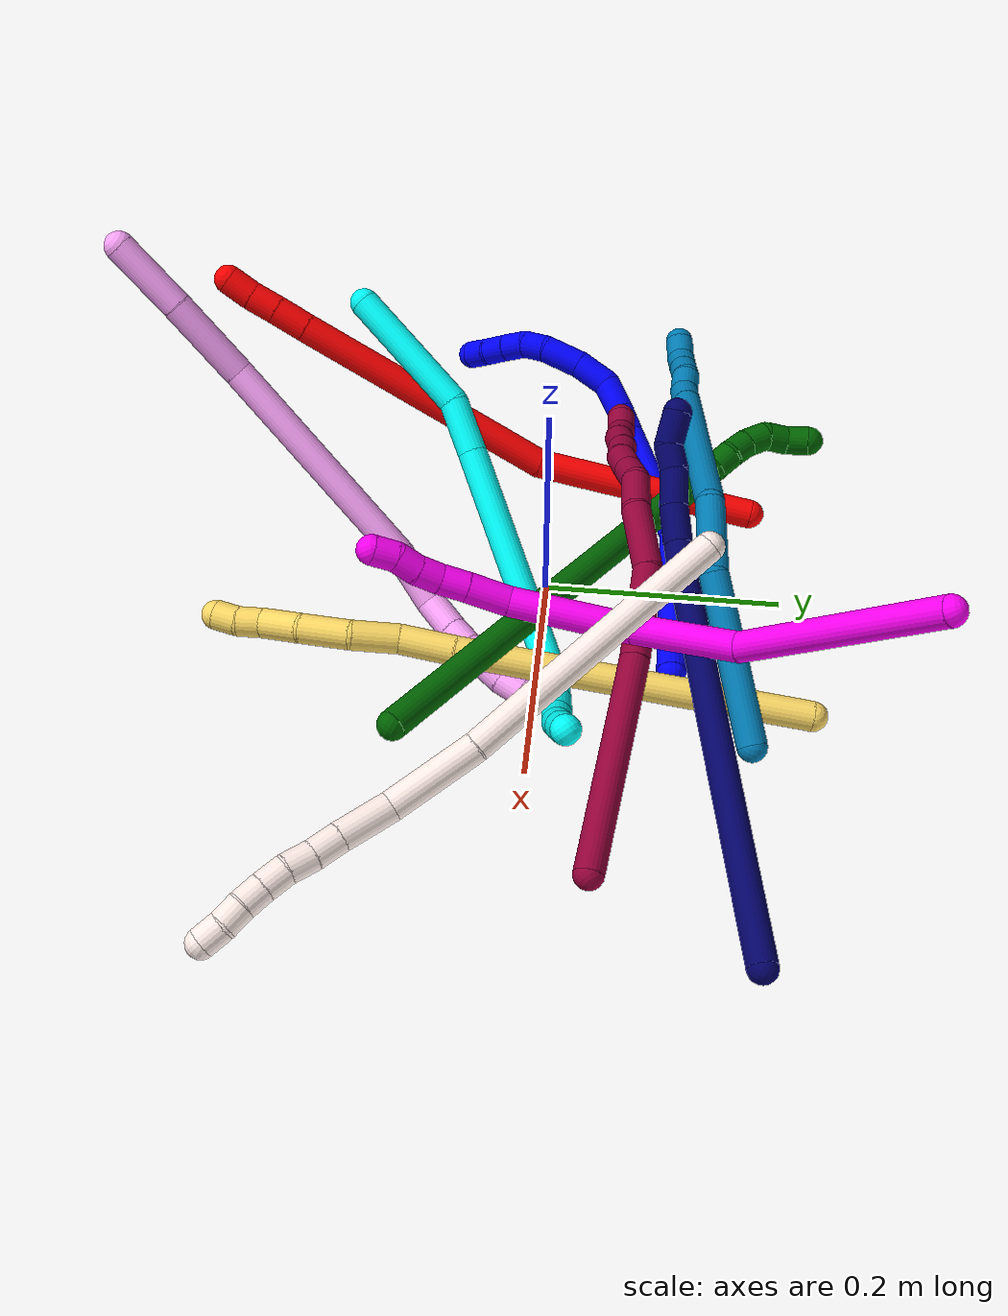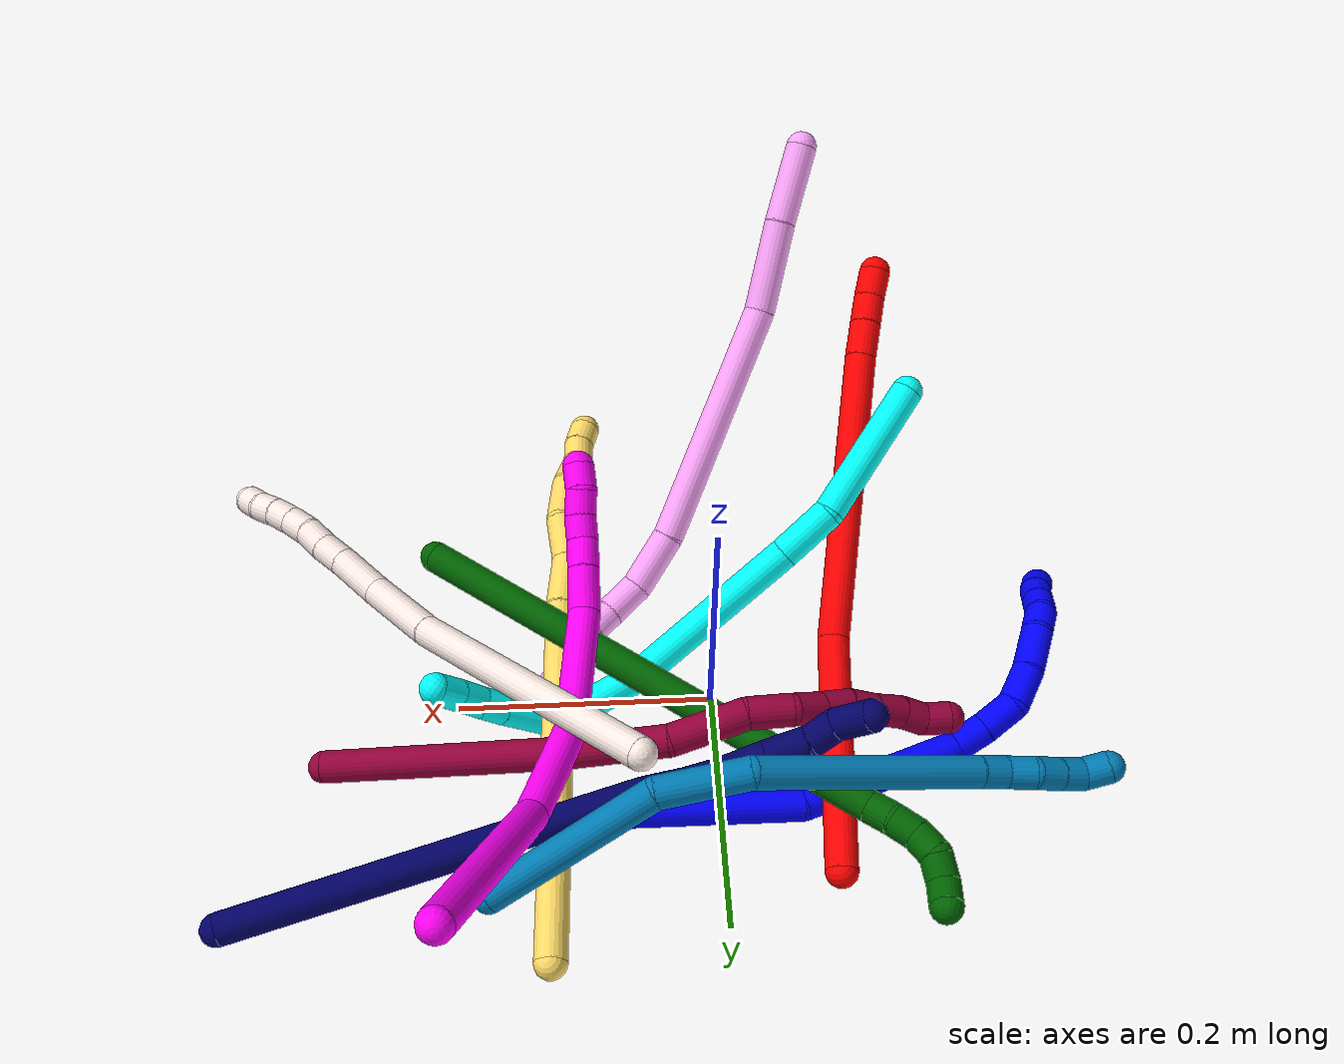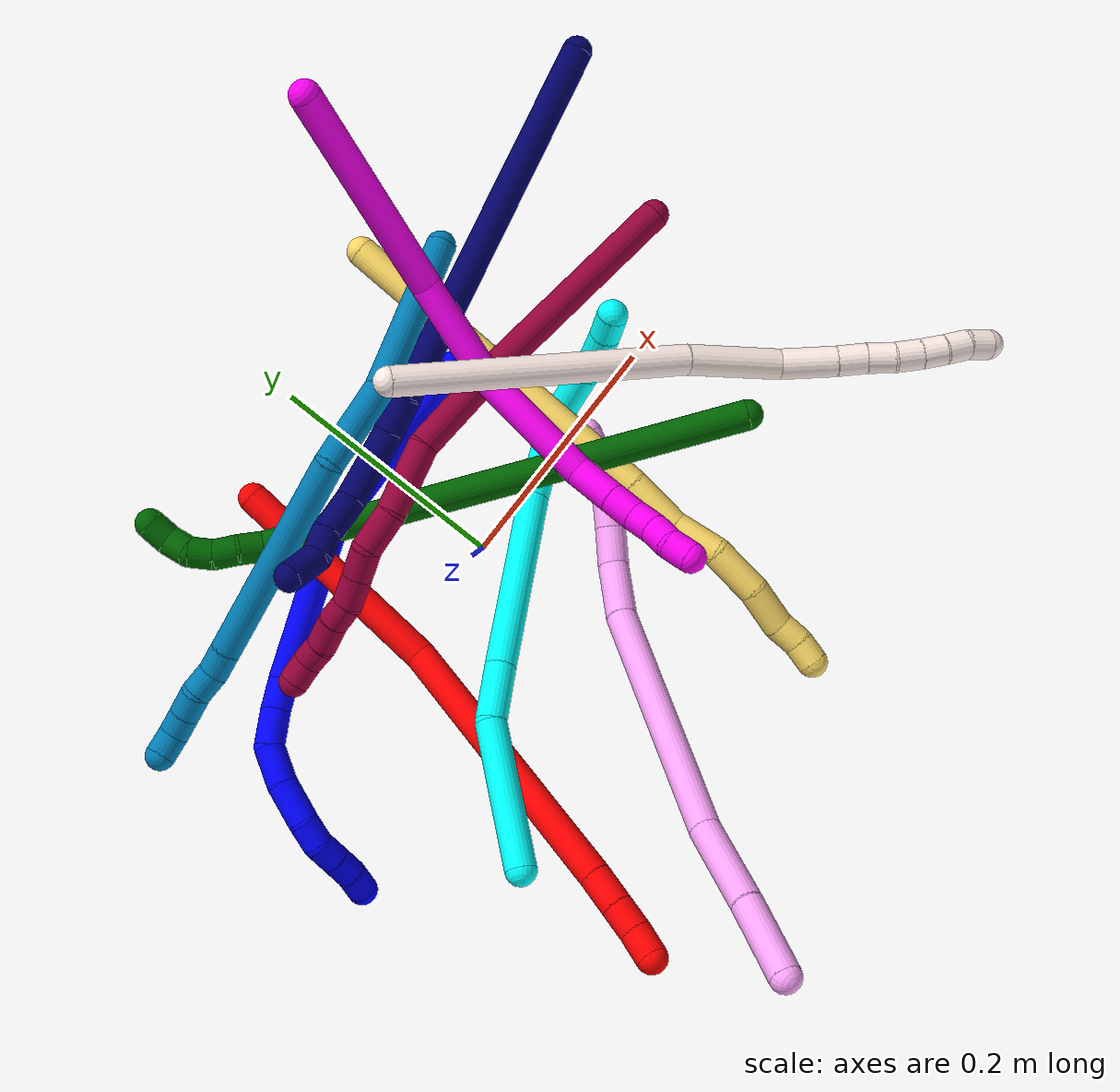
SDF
<sdf version="1.7">
 <world name="default">
  <plugin name="TubeGeneratorPlugin" filename="libtube_generator_plugin.so"/>
  <model name="photoneo_s_sensor">
   <static>1</static>
   <pose>0 0 2 1.57079 1.57079 3.14159</pose>
   <link name="link">
    <inertial><mass>0.1</mass></inertial>
    <sensor name="sensor" type="depth">
     <update_rate>30</update_rate>
     <camera>
      <horizontal_fov>1.22</horizontal_fov>
      <image><width>1920</width><height>1200</height><format>B8G8R8</format></image>
      <clip><near>0.1</near><far>4</far></clip>
      <depth_camera><output>points</output></depth_camera>
     </camera>
     <plugin name="camera_plugin" filename="libgazebo_ros_depth_camera.so">
      <baseline>0.2</baseline>
      <alwaysOn>1</alwaysOn>
      <updateRate>0.0</updateRate>
      <cameraName>camera_ir</cameraName>
      <imageTopicName>/camera/color/image_raw</imageTopicName>
      <cameraInfoTopicName>/camera/color/camera_info</cameraInfoTopicName>
      <depthImageTopicName>/camera/depth/image_raw</depthImageTopicName>
      <depthImageCameraInfoTopicName>/camera/depth/camera_info</depthImageCameraInfoTopicName>
      <pointCloudTopicName>/camera/depth/points</pointCloudTopicName>
      <frameName>fr_optical</frameName>
      <pointCloudCutoff>0.1</pointCloudCutoff>
      <pointCloudCutoffMax>2.0</pointCloudCutoffMax>
      <distortionK1>0</distortionK1>
      <distortionK2>0</distortionK2>
      <distortionK3>0</distortionK3>
      <distortionT1>0</distortionT1>
      <distortionT2>0</distortionT2>
      <CxPrime>0</CxPrime>
      <Cx>0</Cx>
      <Cy>0</Cy>
      <focalLength>0</focalLength>
      <hackBaseline>0</hackBaseline>
     </plugin>
    </sensor>
   </link>
  </model>
  <gravity>0 0 -9.8</gravity>
  <magnetic_field>6e-06 2.3e-05 -4.2e-05</magnetic_field>
  <atmosphere type="adiabatic"/>
  <physics name="default_physics" default="0" type="ode">
   <max_step_size>0.003</max_step_size>
   <real_time_factor>1</real_time_factor>
   <real_time_update_rate>1000</real_time_update_rate>
   <max_contacts>10000</max_contacts>
   <ode>
    <solver>
     <type>quick</type>
     <iters>100</iters>
     <sor>1.3</sor>
     <use_dynamic_moi_rescaling>0</use_dynamic_moi_rescaling>
    </solver>
    <constraints>
     <contact_max_correcting_vel>0</contact_max_correcting_vel>
     <contact_surface_layer>0.001</contact_surface_layer>
     <cfm>0</cfm>
     <erp>0.2</erp>
    </constraints>
   </ode>
  </physics>
  <scene><ambient>0.4 0.4 0.4 1</ambient><background>0.7 0.7 0.7 1</background><shadows>0</shadows></scene>
  <audio><device>default</device></audio>
  <spherical_coordinates>
   <surface_model>EARTH_WGS84</surface_model>
   <latitude_deg>0</latitude_deg>
   <longitude_deg>0</longitude_deg>
   <elevation>0</elevation>
   <heading_deg>0</heading_deg>
  </spherical_coordinates>
  <model name="bin">
   <static>1</static>
   <link name="bottom">
    <collision name="collision-bottom">
     <pose>0 0 -0.01 0 -0 0</pose>
     <geometry><box><size>0.8 0.6 0.02</size></box></geometry>
     <surface>
      <friction><ode><mu>100</mu><mu2>100</mu2></ode></friction>
      <contact><collide_bitmask>65535</collide_bitmask></contact>
     </surface>
    </collision>
   </link>
   <link name="west_wall">
    <collision name="collision-west_wall">
     <pose>-0.41 0 0.1 0 -0 0</pose>
     <geometry><box><size>0.02 0.6 0.2</size></box></geometry>
     <surface>
      <friction><ode><mu>100</mu><mu2>100</mu2></ode></friction>
      <contact><collide_bitmask>65535</collide_bitmask></contact>
     </surface>
    </collision>
   </link>
   <link name="east_wall">
    <collision name="collision-east_wall">
     <pose>0.41 0 0.1 0 -0 0</pose>
     <geometry><box><size>0.02 0.6 0.2</size></box></geometry>
     <surface>
      <friction><ode><mu>100</mu><mu2>100</mu2></ode></friction>
      <contact><collide_bitmask>65535</collide_bitmask></contact>
     </surface>
    </collision>
   </link>
   <link name="south_wall">
    <collision name="collision-south_wall">
     <pose>0 -0.31 0.1 0 -0 0</pose>
     <geometry><box><size>0.8 0.02 0.2</size></box></geometry>
     <surface>
      <friction><ode><mu>100</mu><mu2>100</mu2></ode></friction>
      <contact><collide_bitmask>65535</collide_bitmask></contact>
     </surface>
    </collision>
   </link>
   <link name="north_wall">
    <collision name="collision-north_wall">
     <pose>0 0.31 0.1 0 -0 0</pose>
     <geometry><box><size>0.8 0.02 0.2</size></box></geometry>
     <surface>
      <friction><ode><mu>100</mu><mu2>100</mu2></ode></friction>
      <contact><collide_bitmask>65535</collide_bitmask></contact>
     </surface>
    </collision>
   </link>
  </model>
  <model name="1">
   <static>0</static>
   <link name="1">
    <collision name="collision-cylinder-e_1_1_4">
     <pose>-0.038945 0.006561 0.07103 -0.092112 -0.499745 0.023523</pose>
     <geometry><cylinder><radius>0.0125</radius><length>0.162543</length></cylinder></geometry>
     <surface>
      <friction><ode><mu>1.16</mu><mu2>1.16</mu2><slip1>0</slip1><slip2>0</slip2></ode></friction>
      <contact><ode><kp>1e+06</kp><kd>1</kd><max_vel>0</max_vel><min_depth>0.001</min_depth></ode></contact>
     </surface>
    </collision>
    <visual name="visual-cylinder-e_1_1_4">
     <pose>-0.038945 0.006561 0.07103 -0.092112 -0.499745 0.023523</pose>
     <geometry><cylinder><radius>0.0125</radius><length>0.162543</length></cylinder></geometry>
     <material><ambient>0 0 1 1</ambient></material>
    </visual>
    <collision name="collision-cylinder-e_2_4_5">
     <pose>-0.108729 -0.003254 0.197471 0.287374 -0.490258 -0.072357</pose>
     <geometry><cylinder><radius>0.0125</radius><length>0.130991</length></cylinder></geometry>
     <surface>
      <friction><ode><mu>1.16</mu><mu2>1.16</mu2><slip1>0</slip1><slip2>0</slip2></ode></friction>
      <contact><ode><kp>1e+06</kp><kd>1</kd><max_vel>0</max_vel><min_depth>0.001</min_depth></ode></contact>
     </surface>
    </collision>
    <visual name="visual-cylinder-e_2_4_5">
     <pose>-0.108729 -0.003254 0.197471 0.287374 -0.490258 -0.072357</pose>
     <geometry><cylinder><radius>0.0125</radius><length>0.130991</length></cylinder></geometry>
     <material><ambient>0 0 1 1</ambient></material>
    </visual>
    <collision name="collision-cylinder-e_3_5_6">
     <pose>-0.1423 -0.024518 0.265011 0.382959 -0.205965 -0.040064</pose>
     <geometry><cylinder><radius>0.0125</radius><length>0.026717</length></cylinder></geometry>
     <surface>
      <friction><ode><mu>1.16</mu><mu2>1.16</mu2><slip1>0</slip1><slip2>0</slip2></ode></friction>
      <contact><ode><kp>1e+06</kp><kd>1</kd><max_vel>0</max_vel><min_depth>0.001</min_depth></ode></contact>
     </surface>
    </collision>
    <visual name="visual-cylinder-e_3_5_6">
     <pose>-0.1423 -0.024518 0.265011 0.382959 -0.205965 -0.040064</pose>
     <geometry><cylinder><radius>0.0125</radius><length>0.026717</length></cylinder></geometry>
     <material><ambient>0 0 1 1</ambient></material>
    </visual>
    <collision name="collision-cylinder-e_4_6_7">
     <pose>-0.147279 -0.036108 0.290389 0.468453 -0.150187 -0.035899</pose>
     <geometry><cylinder><radius>0.0125</radius><length>0.030035</length></cylinder></geometry>
     <surface>
      <friction><ode><mu>1.16</mu><mu2>1.16</mu2><slip1>0</slip1><slip2>0</slip2></ode></friction>
      <contact><ode><kp>1e+06</kp><kd>1</kd><max_vel>0</max_vel><min_depth>0.001</min_depth></ode></contact>
     </surface>
    </collision>
    <visual name="visual-cylinder-e_4_6_7">
     <pose>-0.147279 -0.036108 0.290389 0.468453 -0.150187 -0.035899</pose>
     <geometry><cylinder><radius>0.0125</radius><length>0.030035</length></cylinder></geometry>
     <material><ambient>0 0 1 1</ambient></material>
    </visual>
    <collision name="collision-cylinder-e_5_7_8">
     <pose>-0.152121 -0.055835 0.312439 0.976508 -0.163616 -0.087044</pose>
     <geometry><cylinder><radius>0.0125</radius><length>0.031861</length></cylinder></geometry>
     <surface>
      <friction><ode><mu>1.16</mu><mu2>1.16</mu2><slip1>0</slip1><slip2>0</slip2></ode></friction>
      <contact><ode><kp>1e+06</kp><kd>1</kd><max_vel>0</max_vel><min_depth>0.001</min_depth></ode></contact>
     </surface>
    </collision>
    <visual name="visual-cylinder-e_5_7_8">
     <pose>-0.152121 -0.055835 0.312439 0.976508 -0.163616 -0.087044</pose>
     <geometry><cylinder><radius>0.0125</radius><length>0.031861</length></cylinder></geometry>
     <material><ambient>0 0 1 1</ambient></material>
    </visual>
    <collision name="collision-cylinder-e_6_8_9">
     <pose>-0.158314 -0.084832 0.328299 1.15465 -0.20321 -0.132624</pose>
     <geometry><cylinder><radius>0.0125</radius><length>0.035663</length></cylinder></geometry>
     <surface>
      <friction><ode><mu>1.16</mu><mu2>1.16</mu2><slip1>0</slip1><slip2>0</slip2></ode></friction>
      <contact><ode><kp>1e+06</kp><kd>1</kd><max_vel>0</max_vel><min_depth>0.001</min_depth></ode></contact>
     </surface>
    </collision>
    <visual name="visual-cylinder-e_6_8_9">
     <pose>-0.158314 -0.084832 0.328299 1.15465 -0.20321 -0.132624</pose>
     <geometry><cylinder><radius>0.0125</radius><length>0.035663</length></cylinder></geometry>
     <material><ambient>0 0 1 1</ambient></material>
    </visual>
    <collision name="collision-cylinder-e_7_9_10">
     <pose>-0.166601 -0.110007 0.338268 1.26461 -0.452251 -0.333969</pose>
     <geometry><cylinder><radius>0.0125</radius><length>0.021456</length></cylinder></geometry>
     <surface>
      <friction><ode><mu>1.16</mu><mu2>1.16</mu2><slip1>0</slip1><slip2>0</slip2></ode></friction>
      <contact><ode><kp>1e+06</kp><kd>1</kd><max_vel>0</max_vel><min_depth>0.001</min_depth></ode></contact>
     </surface>
    </collision>
    <visual name="visual-cylinder-e_7_9_10">
     <pose>-0.166601 -0.110007 0.338268 1.26461 -0.452251 -0.333969</pose>
     <geometry><cylinder><radius>0.0125</radius><length>0.021456</length></cylinder></geometry>
     <material><ambient>0 0 1 1</ambient></material>
    </visual>
    <collision name="collision-cylinder-e_8_10_11">
     <pose>-0.177473 -0.12734 0.340641 1.63659 -0.649066 -0.689914</pose>
     <geometry><cylinder><radius>0.0125</radius><length>0.020461</length></cylinder></geometry>
     <surface>
      <friction><ode><mu>1.16</mu><mu2>1.16</mu2><slip1>0</slip1><slip2>0</slip2></ode></friction>
      <contact><ode><kp>1e+06</kp><kd>1</kd><max_vel>0</max_vel><min_depth>0.001</min_depth></ode></contact>
     </surface>
    </collision>
    <visual name="visual-cylinder-e_8_10_11">
     <pose>-0.177473 -0.12734 0.340641 1.63659 -0.649066 -0.689914</pose>
     <geometry><cylinder><radius>0.0125</radius><length>0.020461</length></cylinder></geometry>
     <material><ambient>0 0 1 1</ambient></material>
    </visual>
    <collision name="collision-cylinder-e_9_11_12">
     <pose>-0.190091 -0.143174 0.339535 1.64473 -0.694707 -0.74343</pose>
     <geometry><cylinder><radius>0.0125</radius><length>0.020104</length></cylinder></geometry>
     <surface>
      <friction><ode><mu>1.16</mu><mu2>1.16</mu2><slip1>0</slip1><slip2>0</slip2></ode></friction>
      <contact><ode><kp>1e+06</kp><kd>1</kd><max_vel>0</max_vel><min_depth>0.001</min_depth></ode></contact>
     </surface>
    </collision>
    <visual name="visual-cylinder-e_9_11_12">
     <pose>-0.190091 -0.143174 0.339535 1.64473 -0.694707 -0.74343</pose>
     <geometry><cylinder><radius>0.0125</radius><length>0.020104</length></cylinder></geometry>
     <material><ambient>0 0 1 1</ambient></material>
    </visual>
    <collision name="collision-cylinder-e_10_12_2">
     <pose>-0.204156 -0.157439 0.339591 1.47563 -0.858043 -0.788194</pose>
     <geometry><cylinder><radius>0.0125</radius><length>0.02017</length></cylinder></geometry>
     <surface>
      <friction><ode><mu>1.16</mu><mu2>1.16</mu2><slip1>0</slip1><slip2>0</slip2></ode></friction>
      <contact><ode><kp>1e+06</kp><kd>1</kd><max_vel>0</max_vel><min_depth>0.001</min_depth></ode></contact>
     </surface>
    </collision>
    <visual name="visual-cylinder-e_10_12_2">
     <pose>-0.204156 -0.157439 0.339591 1.47563 -0.858043 -0.788194</pose>
     <geometry><cylinder><radius>0.0125</radius><length>0.02017</length></cylinder></geometry>
     <material><ambient>0 0 1 1</ambient></material>
    </visual>
    <collision name="collision-sphere-2">
     <pose>-0.211786 -0.164004 0.340217 0 -0 0</pose>
     <geometry><sphere><radius>0.0125</radius></sphere></geometry>
     <surface>
      <friction><ode><mu>1.16</mu><mu2>1.16</mu2><slip1>0</slip1><slip2>0</slip2></ode></friction>
      <contact><ode><kp>1e+06</kp><kd>1</kd><max_vel>0</max_vel><min_depth>0.001</min_depth></ode></contact>
     </surface>
    </collision>
    <visual name="visual-sphere-2">
     <pose>-0.211786 -0.164004 0.340217 0 -0 0</pose>
     <geometry><sphere><radius>0.0125</radius></sphere></geometry>
     <material><ambient>0 0 1 1</ambient></material>
    </visual>
    <collision name="collision-sphere-12">
     <pose>-0.196526 -0.150875 0.338964 0 -0 0</pose>
     <geometry><sphere><radius>0.0125</radius></sphere></geometry>
     <surface>
      <friction><ode><mu>1.16</mu><mu2>1.16</mu2><slip1>0</slip1><slip2>0</slip2></ode></friction>
      <contact><ode><kp>1e+06</kp><kd>1</kd><max_vel>0</max_vel><min_depth>0.001</min_depth></ode></contact>
     </surface>
    </collision>
    <visual name="visual-sphere-12">
     <pose>-0.196526 -0.150875 0.338964 0 -0 0</pose>
     <geometry><sphere><radius>0.0125</radius></sphere></geometry>
     <material><ambient>0 0 1 1</ambient></material>
    </visual>
    <collision name="collision-sphere-11">
     <pose>-0.183657 -0.135472 0.340105 0 -0 0</pose>
     <geometry><sphere><radius>0.0125</radius></sphere></geometry>
     <surface>
      <friction><ode><mu>1.16</mu><mu2>1.16</mu2><slip1>0</slip1><slip2>0</slip2></ode></friction>
      <contact><ode><kp>1e+06</kp><kd>1</kd><max_vel>0</max_vel><min_depth>0.001</min_depth></ode></contact>
     </surface>
    </collision>
    <visual name="visual-sphere-11">
     <pose>-0.183657 -0.135472 0.340105 0 -0 0</pose>
     <geometry><sphere><radius>0.0125</radius></sphere></geometry>
     <material><ambient>0 0 1 1</ambient></material>
    </visual>
    <collision name="collision-sphere-10">
     <pose>-0.171289 -0.119208 0.341177 0 -0 0</pose>
     <geometry><sphere><radius>0.0125</radius></sphere></geometry>
     <surface>
      <friction><ode><mu>1.16</mu><mu2>1.16</mu2><slip1>0</slip1><slip2>0</slip2></ode></friction>
      <contact><ode><kp>1e+06</kp><kd>1</kd><max_vel>0</max_vel><min_depth>0.001</min_depth></ode></contact>
     </surface>
    </collision>
    <visual name="visual-sphere-10">
     <pose>-0.171289 -0.119208 0.341177 0 -0 0</pose>
     <geometry><sphere><radius>0.0125</radius></sphere></geometry>
     <material><ambient>0 0 1 1</ambient></material>
    </visual>
    <collision name="collision-sphere-9">
     <pose>-0.161913 -0.100806 0.335359 0 -0 0</pose>
     <geometry><sphere><radius>0.0125</radius></sphere></geometry>
     <surface>
      <friction><ode><mu>1.16</mu><mu2>1.16</mu2><slip1>0</slip1><slip2>0</slip2></ode></friction>
      <contact><ode><kp>1e+06</kp><kd>1</kd><max_vel>0</max_vel><min_depth>0.001</min_depth></ode></contact>
     </surface>
    </collision>
    <visual name="visual-sphere-9">
     <pose>-0.161913 -0.100806 0.335359 0 -0 0</pose>
     <geometry><sphere><radius>0.0125</radius></sphere></geometry>
     <material><ambient>0 0 1 1</ambient></material>
    </visual>
    <collision name="collision-sphere-4">
     <pose>-0.077891 0.013123 0.14206 0 -0 0</pose>
     <geometry><sphere><radius>0.0125</radius></sphere></geometry>
     <surface>
      <friction><ode><mu>1.16</mu><mu2>1.16</mu2><slip1>0</slip1><slip2>0</slip2></ode></friction>
      <contact><ode><kp>1e+06</kp><kd>1</kd><max_vel>0</max_vel><min_depth>0.001</min_depth></ode></contact>
     </surface>
    </collision>
    <visual name="visual-sphere-4">
     <pose>-0.077891 0.013123 0.14206 0 -0 0</pose>
     <geometry><sphere><radius>0.0125</radius></sphere></geometry>
     <material><ambient>0 0 1 1</ambient></material>
    </visual>
    <collision name="collision-sphere-1">
     <geometry><sphere><radius>0.0125</radius></sphere></geometry>
     <surface>
      <friction><ode><mu>1.16</mu><mu2>1.16</mu2><slip1>0</slip1><slip2>0</slip2></ode></friction>
      <contact><ode><kp>1e+06</kp><kd>1</kd><max_vel>0</max_vel><min_depth>0.001</min_depth></ode></contact>
     </surface>
    </collision>
    <visual name="visual-sphere-1">
     <geometry><sphere><radius>0.0125</radius></sphere></geometry>
     <material><ambient>0 0 1 1</ambient></material>
    </visual>
    <collision name="collision-sphere-8">
     <pose>-0.154716 -0.068858 0.321239 0 -0 0</pose>
     <geometry><sphere><radius>0.0125</radius></sphere></geometry>
     <surface>
      <friction><ode><mu>1.16</mu><mu2>1.16</mu2><slip1>0</slip1><slip2>0</slip2></ode></friction>
      <contact><ode><kp>1e+06</kp><kd>1</kd><max_vel>0</max_vel><min_depth>0.001</min_depth></ode></contact>
     </surface>
    </collision>
    <visual name="visual-sphere-8">
     <pose>-0.154716 -0.068858 0.321239 0 -0 0</pose>
     <geometry><sphere><radius>0.0125</radius></sphere></geometry>
     <material><ambient>0 0 1 1</ambient></material>
    </visual>
    <collision name="collision-sphere-5">
     <pose>-0.139568 -0.019632 0.252882 0 -0 0</pose>
     <geometry><sphere><radius>0.0125</radius></sphere></geometry>
     <surface>
      <friction><ode><mu>1.16</mu><mu2>1.16</mu2><slip1>0</slip1><slip2>0</slip2></ode></friction>
      <contact><ode><kp>1e+06</kp><kd>1</kd><max_vel>0</max_vel><min_depth>0.001</min_depth></ode></contact>
     </surface>
    </collision>
    <visual name="visual-sphere-5">
     <pose>-0.139568 -0.019632 0.252882 0 -0 0</pose>
     <geometry><sphere><radius>0.0125</radius></sphere></geometry>
     <material><ambient>0 0 1 1</ambient></material>
    </visual>
    <collision name="collision-sphere-6">
     <pose>-0.145032 -0.029404 0.27714 0 -0 0</pose>
     <geometry><sphere><radius>0.0125</radius></sphere></geometry>
     <surface>
      <friction><ode><mu>1.16</mu><mu2>1.16</mu2><slip1>0</slip1><slip2>0</slip2></ode></friction>
      <contact><ode><kp>1e+06</kp><kd>1</kd><max_vel>0</max_vel><min_depth>0.001</min_depth></ode></contact>
     </surface>
    </collision>
    <visual name="visual-sphere-6">
     <pose>-0.145032 -0.029404 0.27714 0 -0 0</pose>
     <geometry><sphere><radius>0.0125</radius></sphere></geometry>
     <material><ambient>0 0 1 1</ambient></material>
    </visual>
    <collision name="collision-sphere-7">
     <pose>-0.149526 -0.042812 0.303638 0 -0 0</pose>
     <geometry><sphere><radius>0.0125</radius></sphere></geometry>
     <surface>
      <friction><ode><mu>1.16</mu><mu2>1.16</mu2><slip1>0</slip1><slip2>0</slip2></ode></friction>
      <contact><ode><kp>1e+06</kp><kd>1</kd><max_vel>0</max_vel><min_depth>0.001</min_depth></ode></contact>
     </surface>
    </collision>
    <visual name="visual-sphere-7">
     <pose>-0.149526 -0.042812 0.303638 0 -0 0</pose>
     <geometry><sphere><radius>0.0125</radius></sphere></geometry>
     <material><ambient>0 0 1 1</ambient></material>
    </visual>
    <inertial>
     <pose>-0.108872 -0.033847 0.205561 0 -0 0</pose>
     <mass>0.5</mass>
     <inertia>
      <ixx>0.000482</ixx>
      <ixy>0</ixy>
      <ixz>0</ixz>
      <iyy>0.00054</iyy>
      <iyz>0</iyz>
      <izz>0.000332</izz>
     </inertia>
    </inertial>
   </link>
   <pose>0.099969 0.111506 0.01954 -0.379564 -1.07501 0.438994</pose>
  </model>
  <model name="2">
   <static>0</static>
   <link name="2">
    <collision name="collision-cylinder-e_1_1_4">
     <pose>0.003129 -0.086781 0.037399 1.16389 0.033098 0.021778</pose>
     <geometry><cylinder><radius>0.0125</radius><length>0.189097</length></cylinder></geometry>
     <surface>
      <friction><ode><mu>1.16</mu><mu2>1.16</mu2><slip1>0</slip1><slip2>0</slip2></ode></friction>
      <contact><ode><kp>1e+06</kp><kd>1</kd><max_vel>0</max_vel><min_depth>0.001</min_depth></ode></contact>
     </surface>
    </collision>
    <visual name="visual-cylinder-e_1_1_4">
     <pose>0.003129 -0.086781 0.037399 1.16389 0.033098 0.021778</pose>
     <geometry><cylinder><radius>0.0125</radius><length>0.189097</length></cylinder></geometry>
     <material><ambient>1 0 0 1</ambient></material>
    </visual>
    <collision name="collision-cylinder-e_2_4_5">
     <pose>-0.01474 -0.265392 0.144421 0.92209 -0.18023 -0.089712</pose>
     <geometry><cylinder><radius>0.0125</radius><length>0.234273</length></cylinder></geometry>
     <surface>
      <friction><ode><mu>1.16</mu><mu2>1.16</mu2><slip1>0</slip1><slip2>0</slip2></ode></friction>
      <contact><ode><kp>1e+06</kp><kd>1</kd><max_vel>0</max_vel><min_depth>0.001</min_depth></ode></contact>
     </surface>
    </collision>
    <visual name="visual-cylinder-e_2_4_5">
     <pose>-0.01474 -0.265392 0.144421 0.92209 -0.18023 -0.089712</pose>
     <geometry><cylinder><radius>0.0125</radius><length>0.234273</length></cylinder></geometry>
     <material><ambient>1 0 0 1</ambient></material>
    </visual>
    <collision name="collision-cylinder-e_3_5_6">
     <pose>-0.03885 -0.368869 0.222274 0.955575 -0.214936 -0.111609</pose>
     <geometry><cylinder><radius>0.0125</radius><length>0.029194</length></cylinder></geometry>
     <surface>
      <friction><ode><mu>1.16</mu><mu2>1.16</mu2><slip1>0</slip1><slip2>0</slip2></ode></friction>
      <contact><ode><kp>1e+06</kp><kd>1</kd><max_vel>0</max_vel><min_depth>0.001</min_depth></ode></contact>
     </surface>
    </collision>
    <visual name="visual-cylinder-e_3_5_6">
     <pose>-0.03885 -0.368869 0.222274 0.955575 -0.214936 -0.111609</pose>
     <geometry><cylinder><radius>0.0125</radius><length>0.029194</length></cylinder></geometry>
     <material><ambient>1 0 0 1</ambient></material>
    </visual>
    <collision name="collision-cylinder-e_4_6_7">
     <pose>-0.044381 -0.390292 0.236802 0.998625 -0.204908 -0.112034</pose>
     <geometry><cylinder><radius>0.0125</radius><length>0.023756</length></cylinder></geometry>
     <surface>
      <friction><ode><mu>1.16</mu><mu2>1.16</mu2><slip1>0</slip1><slip2>0</slip2></ode></friction>
      <contact><ode><kp>1e+06</kp><kd>1</kd><max_vel>0</max_vel><min_depth>0.001</min_depth></ode></contact>
     </surface>
    </collision>
    <visual name="visual-cylinder-e_4_6_7">
     <pose>-0.044381 -0.390292 0.236802 0.998625 -0.204908 -0.112034</pose>
     <geometry><cylinder><radius>0.0125</radius><length>0.023756</length></cylinder></geometry>
     <material><ambient>1 0 0 1</ambient></material>
    </visual>
    <collision name="collision-cylinder-e_5_7_2">
     <pose>-0.050156 -0.409156 0.249906 0.927859 -0.287612 -0.144655</pose>
     <geometry><cylinder><radius>0.0125</radius><length>0.02368</length></cylinder></geometry>
     <surface>
      <friction><ode><mu>1.16</mu><mu2>1.16</mu2><slip1>0</slip1><slip2>0</slip2></ode></friction>
      <contact><ode><kp>1e+06</kp><kd>1</kd><max_vel>0</max_vel><min_depth>0.001</min_depth></ode></contact>
     </surface>
    </collision>
    <visual name="visual-cylinder-e_5_7_2">
     <pose>-0.050156 -0.409156 0.249906 0.927859 -0.287612 -0.144655</pose>
     <geometry><cylinder><radius>0.0125</radius><length>0.02368</length></cylinder></geometry>
     <material><ambient>1 0 0 1</ambient></material>
    </visual>
    <collision name="collision-sphere-2">
     <pose>-0.053515 -0.418243 0.256713 0 -0 0</pose>
     <geometry><sphere><radius>0.0125</radius></sphere></geometry>
     <surface>
      <friction><ode><mu>1.16</mu><mu2>1.16</mu2><slip1>0</slip1><slip2>0</slip2></ode></friction>
      <contact><ode><kp>1e+06</kp><kd>1</kd><max_vel>0</max_vel><min_depth>0.001</min_depth></ode></contact>
     </surface>
    </collision>
    <visual name="visual-sphere-2">
     <pose>-0.053515 -0.418243 0.256713 0 -0 0</pose>
     <geometry><sphere><radius>0.0125</radius></sphere></geometry>
     <material><ambient>1 0 0 1</ambient></material>
    </visual>
    <collision name="collision-sphere-7">
     <pose>-0.046798 -0.40007 0.243099 0 -0 0</pose>
     <geometry><sphere><radius>0.0125</radius></sphere></geometry>
     <surface>
      <friction><ode><mu>1.16</mu><mu2>1.16</mu2><slip1>0</slip1><slip2>0</slip2></ode></friction>
      <contact><ode><kp>1e+06</kp><kd>1</kd><max_vel>0</max_vel><min_depth>0.001</min_depth></ode></contact>
     </surface>
    </collision>
    <visual name="visual-sphere-7">
     <pose>-0.046798 -0.40007 0.243099 0 -0 0</pose>
     <geometry><sphere><radius>0.0125</radius></sphere></geometry>
     <material><ambient>1 0 0 1</ambient></material>
    </visual>
    <collision name="collision-sphere-6">
     <pose>-0.041964 -0.380515 0.230505 0 -0 0</pose>
     <geometry><sphere><radius>0.0125</radius></sphere></geometry>
     <surface>
      <friction><ode><mu>1.16</mu><mu2>1.16</mu2><slip1>0</slip1><slip2>0</slip2></ode></friction>
      <contact><ode><kp>1e+06</kp><kd>1</kd><max_vel>0</max_vel><min_depth>0.001</min_depth></ode></contact>
     </surface>
    </collision>
    <visual name="visual-sphere-6">
     <pose>-0.041964 -0.380515 0.230505 0 -0 0</pose>
     <geometry><sphere><radius>0.0125</radius></sphere></geometry>
     <material><ambient>1 0 0 1</ambient></material>
    </visual>
    <collision name="collision-sphere-5">
     <pose>-0.035737 -0.357223 0.214043 0 -0 0</pose>
     <geometry><sphere><radius>0.0125</radius></sphere></geometry>
     <surface>
      <friction><ode><mu>1.16</mu><mu2>1.16</mu2><slip1>0</slip1><slip2>0</slip2></ode></friction>
      <contact><ode><kp>1e+06</kp><kd>1</kd><max_vel>0</max_vel><min_depth>0.001</min_depth></ode></contact>
     </surface>
    </collision>
    <visual name="visual-sphere-5">
     <pose>-0.035737 -0.357223 0.214043 0 -0 0</pose>
     <geometry><sphere><radius>0.0125</radius></sphere></geometry>
     <material><ambient>1 0 0 1</ambient></material>
    </visual>
    <collision name="collision-sphere-1">
     <geometry><sphere><radius>0.0125</radius></sphere></geometry>
     <surface>
      <friction><ode><mu>1.16</mu><mu2>1.16</mu2><slip1>0</slip1><slip2>0</slip2></ode></friction>
      <contact><ode><kp>1e+06</kp><kd>1</kd><max_vel>0</max_vel><min_depth>0.001</min_depth></ode></contact>
     </surface>
    </collision>
    <visual name="visual-sphere-1">
     <geometry><sphere><radius>0.0125</radius></sphere></geometry>
     <material><ambient>1 0 0 1</ambient></material>
    </visual>
    <collision name="collision-sphere-4">
     <pose>0.006258 -0.173562 0.074798 0 -0 0</pose>
     <geometry><sphere><radius>0.0125</radius></sphere></geometry>
     <surface>
      <friction><ode><mu>1.16</mu><mu2>1.16</mu2><slip1>0</slip1><slip2>0</slip2></ode></friction>
      <contact><ode><kp>1e+06</kp><kd>1</kd><max_vel>0</max_vel><min_depth>0.001</min_depth></ode></contact>
     </surface>
    </collision>
    <visual name="visual-sphere-4">
     <pose>0.006258 -0.173562 0.074798 0 -0 0</pose>
     <geometry><sphere><radius>0.0125</radius></sphere></geometry>
     <material><ambient>1 0 0 1</ambient></material>
    </visual>
    <inertial>
     <pose>-0.012475 -0.216627 0.117876 0 -0 0</pose>
     <mass>0.5</mass>
     <inertia>
      <ixx>0.001548</ixx>
      <ixy>0</ixy>
      <ixz>0</ixz>
      <iyy>0.000778</iyy>
      <iyz>0</iyz>
      <izz>0.001573</izz>
     </inertia>
    </inertial>
   </link>
   <pose>-0.08269 0.171013 0.023762 0.215011 0.399755 -0.177236</pose>
  </model>
  <model name="3">
   <static>0</static>
   <link name="3">
    <collision name="collision-cylinder-e_1_1_4">
     <pose>-0.000265 0.009664 -0.058177 -2.97699 -0.004485 0.054362</pose>
     <geometry><cylinder><radius>0.0125</radius><length>0.117949</length></cylinder></geometry>
     <surface>
      <friction><ode><mu>1.16</mu><mu2>1.16</mu2><slip1>0</slip1><slip2>0</slip2></ode></friction>
      <contact><ode><kp>1e+06</kp><kd>1</kd><max_vel>0</max_vel><min_depth>0.001</min_depth></ode></contact>
     </surface>
    </collision>
    <visual name="visual-cylinder-e_1_1_4">
     <pose>-0.000265 0.009664 -0.058177 -2.97699 -0.004485 0.054362</pose>
     <geometry><cylinder><radius>0.0125</radius><length>0.117949</length></cylinder></geometry>
     <material><ambient>0.003922 1 0.996078 1</ambient></material>
    </visual>
    <collision name="collision-cylinder-e_2_4_5">
     <pose>0.004504 0.016183 -0.139284 3.00531 0.214122 2.01007</pose>
     <geometry><cylinder><radius>0.0125</radius><length>0.047372</length></cylinder></geometry>
     <surface>
      <friction><ode><mu>1.16</mu><mu2>1.16</mu2><slip1>0</slip1><slip2>0</slip2></ode></friction>
      <contact><ode><kp>1e+06</kp><kd>1</kd><max_vel>0</max_vel><min_depth>0.001</min_depth></ode></contact>
     </surface>
    </collision>
    <visual name="visual-cylinder-e_2_4_5">
     <pose>0.004504 0.016183 -0.139284 3.00531 0.214122 2.01007</pose>
     <geometry><cylinder><radius>0.0125</radius><length>0.047372</length></cylinder></geometry>
     <material><ambient>0.003922 1 0.996078 1</ambient></material>
    </visual>
    <collision name="collision-cylinder-e_3_5_6">
     <pose>0.028724 0.004519 -0.235267 3.0255 0.255192 2.29096</pose>
     <geometry><cylinder><radius>0.0125</radius><length>0.152017</length></cylinder></geometry>
     <surface>
      <friction><ode><mu>1.16</mu><mu2>1.16</mu2><slip1>0</slip1><slip2>0</slip2></ode></friction>
      <contact><ode><kp>1e+06</kp><kd>1</kd><max_vel>0</max_vel><min_depth>0.001</min_depth></ode></contact>
     </surface>
    </collision>
    <visual name="visual-cylinder-e_3_5_6">
     <pose>0.028724 0.004519 -0.235267 3.0255 0.255192 2.29096</pose>
     <geometry><cylinder><radius>0.0125</radius><length>0.152017</length></cylinder></geometry>
     <material><ambient>0.003922 1 0.996078 1</ambient></material>
    </visual>
    <collision name="collision-cylinder-e_4_6_7">
     <pose>0.060473 -0.002747 -0.33364 -3.09214 0.460044 -2.93116</pose>
     <geometry><cylinder><radius>0.0125</radius><length>0.056588</length></cylinder></geometry>
     <surface>
      <friction><ode><mu>1.16</mu><mu2>1.16</mu2><slip1>0</slip1><slip2>0</slip2></ode></friction>
      <contact><ode><kp>1e+06</kp><kd>1</kd><max_vel>0</max_vel><min_depth>0.001</min_depth></ode></contact>
     </surface>
    </collision>
    <visual name="visual-cylinder-e_4_6_7">
     <pose>0.060473 -0.002747 -0.33364 -3.09214 0.460044 -2.93116</pose>
     <geometry><cylinder><radius>0.0125</radius><length>0.056588</length></cylinder></geometry>
     <material><ambient>0.003922 1 0.996078 1</ambient></material>
    </visual>
    <collision name="collision-cylinder-e_5_7_8">
     <pose>0.08195 -0.000119 -0.36739 -2.97993 0.806883 -2.76651</pose>
     <geometry><cylinder><radius>0.0125</radius><length>0.024689</length></cylinder></geometry>
     <surface>
      <friction><ode><mu>1.16</mu><mu2>1.16</mu2><slip1>0</slip1><slip2>0</slip2></ode></friction>
      <contact><ode><kp>1e+06</kp><kd>1</kd><max_vel>0</max_vel><min_depth>0.001</min_depth></ode></contact>
     </surface>
    </collision>
    <visual name="visual-cylinder-e_5_7_8">
     <pose>0.08195 -0.000119 -0.36739 -2.97993 0.806883 -2.76651</pose>
     <geometry><cylinder><radius>0.0125</radius><length>0.024689</length></cylinder></geometry>
     <material><ambient>0.003922 1 0.996078 1</ambient></material>
    </visual>
    <collision name="collision-cylinder-e_6_8_9">
     <pose>0.106048 0.008321 -0.380789 -2.18384 1.05349 -1.684</pose>
     <geometry><cylinder><radius>0.0125</radius><length>0.034937</length></cylinder></geometry>
     <surface>
      <friction><ode><mu>1.16</mu><mu2>1.16</mu2><slip1>0</slip1><slip2>0</slip2></ode></friction>
      <contact><ode><kp>1e+06</kp><kd>1</kd><max_vel>0</max_vel><min_depth>0.001</min_depth></ode></contact>
     </surface>
    </collision>
    <visual name="visual-cylinder-e_6_8_9">
     <pose>0.106048 0.008321 -0.380789 -2.18384 1.05349 -1.684</pose>
     <geometry><cylinder><radius>0.0125</radius><length>0.034937</length></cylinder></geometry>
     <material><ambient>0.003922 1 0.996078 1</ambient></material>
    </visual>
    <collision name="collision-cylinder-e_7_9_10">
     <pose>0.130296 0.020047 -0.388128 -2.04105 1.04775 -1.51078</pose>
     <geometry><cylinder><radius>0.0125</radius><length>0.02093</length></cylinder></geometry>
     <surface>
      <friction><ode><mu>1.16</mu><mu2>1.16</mu2><slip1>0</slip1><slip2>0</slip2></ode></friction>
      <contact><ode><kp>1e+06</kp><kd>1</kd><max_vel>0</max_vel><min_depth>0.001</min_depth></ode></contact>
     </surface>
    </collision>
    <visual name="visual-cylinder-e_7_9_10">
     <pose>0.130296 0.020047 -0.388128 -2.04105 1.04775 -1.51078</pose>
     <geometry><cylinder><radius>0.0125</radius><length>0.02093</length></cylinder></geometry>
     <material><ambient>0.003922 1 0.996078 1</ambient></material>
    </visual>
    <collision name="collision-cylinder-e_8_10_11">
     <pose>0.148545 0.031755 -0.39228 -1.81868 0.901112 -1.11205</pose>
     <geometry><cylinder><radius>0.0125</radius><length>0.023425</length></cylinder></geometry>
     <surface>
      <friction><ode><mu>1.16</mu><mu2>1.16</mu2><slip1>0</slip1><slip2>0</slip2></ode></friction>
      <contact><ode><kp>1e+06</kp><kd>1</kd><max_vel>0</max_vel><min_depth>0.001</min_depth></ode></contact>
     </surface>
    </collision>
    <visual name="visual-cylinder-e_8_10_11">
     <pose>0.148545 0.031755 -0.39228 -1.81868 0.901112 -1.11205</pose>
     <geometry><cylinder><radius>0.0125</radius><length>0.023425</length></cylinder></geometry>
     <material><ambient>0.003922 1 0.996078 1</ambient></material>
    </visual>
    <collision name="collision-cylinder-e_9_11_2">
     <pose>0.166035 0.045795 -0.39609 -1.85285 0.851253 -1.08577</pose>
     <geometry><cylinder><radius>0.0125</radius><length>0.022092</length></cylinder></geometry>
     <surface>
      <friction><ode><mu>1.16</mu><mu2>1.16</mu2><slip1>0</slip1><slip2>0</slip2></ode></friction>
      <contact><ode><kp>1e+06</kp><kd>1</kd><max_vel>0</max_vel><min_depth>0.001</min_depth></ode></contact>
     </surface>
    </collision>
    <visual name="visual-cylinder-e_9_11_2">
     <pose>0.166035 0.045795 -0.39609 -1.85285 0.851253 -1.08577</pose>
     <geometry><cylinder><radius>0.0125</radius><length>0.022092</length></cylinder></geometry>
     <material><ambient>0.003922 1 0.996078 1</ambient></material>
    </visual>
    <collision name="collision-sphere-2">
     <pose>0.174343 0.052787 -0.398116 0 -0 0</pose>
     <geometry><sphere><radius>0.0125</radius></sphere></geometry>
     <surface>
      <friction><ode><mu>1.16</mu><mu2>1.16</mu2><slip1>0</slip1><slip2>0</slip2></ode></friction>
      <contact><ode><kp>1e+06</kp><kd>1</kd><max_vel>0</max_vel><min_depth>0.001</min_depth></ode></contact>
     </surface>
    </collision>
    <visual name="visual-sphere-2">
     <pose>0.174343 0.052787 -0.398116 0 -0 0</pose>
     <geometry><sphere><radius>0.0125</radius></sphere></geometry>
     <material><ambient>0.003922 1 0.996078 1</ambient></material>
    </visual>
    <collision name="collision-sphere-11">
     <pose>0.157727 0.038803 -0.394064 0 -0 0</pose>
     <geometry><sphere><radius>0.0125</radius></sphere></geometry>
     <surface>
      <friction><ode><mu>1.16</mu><mu2>1.16</mu2><slip1>0</slip1><slip2>0</slip2></ode></friction>
      <contact><ode><kp>1e+06</kp><kd>1</kd><max_vel>0</max_vel><min_depth>0.001</min_depth></ode></contact>
     </surface>
    </collision>
    <visual name="visual-sphere-11">
     <pose>0.157727 0.038803 -0.394064 0 -0 0</pose>
     <geometry><sphere><radius>0.0125</radius></sphere></geometry>
     <material><ambient>0.003922 1 0.996078 1</ambient></material>
    </visual>
    <collision name="collision-sphere-10">
     <pose>0.139362 0.024707 -0.390496 0 -0 0</pose>
     <geometry><sphere><radius>0.0125</radius></sphere></geometry>
     <surface>
      <friction><ode><mu>1.16</mu><mu2>1.16</mu2><slip1>0</slip1><slip2>0</slip2></ode></friction>
      <contact><ode><kp>1e+06</kp><kd>1</kd><max_vel>0</max_vel><min_depth>0.001</min_depth></ode></contact>
     </surface>
    </collision>
    <visual name="visual-sphere-10">
     <pose>0.139362 0.024707 -0.390496 0 -0 0</pose>
     <geometry><sphere><radius>0.0125</radius></sphere></geometry>
     <material><ambient>0.003922 1 0.996078 1</ambient></material>
    </visual>
    <collision name="collision-sphere-9">
     <pose>0.121231 0.015387 -0.385759 0 -0 0</pose>
     <geometry><sphere><radius>0.0125</radius></sphere></geometry>
     <surface>
      <friction><ode><mu>1.16</mu><mu2>1.16</mu2><slip1>0</slip1><slip2>0</slip2></ode></friction>
      <contact><ode><kp>1e+06</kp><kd>1</kd><max_vel>0</max_vel><min_depth>0.001</min_depth></ode></contact>
     </surface>
    </collision>
    <visual name="visual-sphere-9">
     <pose>0.121231 0.015387 -0.385759 0 -0 0</pose>
     <geometry><sphere><radius>0.0125</radius></sphere></geometry>
     <material><ambient>0.003922 1 0.996078 1</ambient></material>
    </visual>
    <collision name="collision-sphere-4">
     <pose>-0.000529 0.019327 -0.116353 0 -0 0</pose>
     <geometry><sphere><radius>0.0125</radius></sphere></geometry>
     <surface>
      <friction><ode><mu>1.16</mu><mu2>1.16</mu2><slip1>0</slip1><slip2>0</slip2></ode></friction>
      <contact><ode><kp>1e+06</kp><kd>1</kd><max_vel>0</max_vel><min_depth>0.001</min_depth></ode></contact>
     </surface>
    </collision>
    <visual name="visual-sphere-4">
     <pose>-0.000529 0.019327 -0.116353 0 -0 0</pose>
     <geometry><sphere><radius>0.0125</radius></sphere></geometry>
     <material><ambient>0.003922 1 0.996078 1</ambient></material>
    </visual>
    <collision name="collision-sphere-1">
     <geometry><sphere><radius>0.0125</radius></sphere></geometry>
     <surface>
      <friction><ode><mu>1.16</mu><mu2>1.16</mu2><slip1>0</slip1><slip2>0</slip2></ode></friction>
      <contact><ode><kp>1e+06</kp><kd>1</kd><max_vel>0</max_vel><min_depth>0.001</min_depth></ode></contact>
     </surface>
    </collision>
    <visual name="visual-sphere-1">
     <geometry><sphere><radius>0.0125</radius></sphere></geometry>
     <material><ambient>0.003922 1 0.996078 1</ambient></material>
    </visual>
    <collision name="collision-sphere-8">
     <pose>0.090865 0.001255 -0.375818 0 -0 0</pose>
     <geometry><sphere><radius>0.0125</radius></sphere></geometry>
     <surface>
      <friction><ode><mu>1.16</mu><mu2>1.16</mu2><slip1>0</slip1><slip2>0</slip2></ode></friction>
      <contact><ode><kp>1e+06</kp><kd>1</kd><max_vel>0</max_vel><min_depth>0.001</min_depth></ode></contact>
     </surface>
    </collision>
    <visual name="visual-sphere-8">
     <pose>0.090865 0.001255 -0.375818 0 -0 0</pose>
     <geometry><sphere><radius>0.0125</radius></sphere></geometry>
     <material><ambient>0.003922 1 0.996078 1</ambient></material>
    </visual>
    <collision name="collision-sphere-5">
     <pose>0.009537 0.013038 -0.162215 0 -0 0</pose>
     <geometry><sphere><radius>0.0125</radius></sphere></geometry>
     <surface>
      <friction><ode><mu>1.16</mu><mu2>1.16</mu2><slip1>0</slip1><slip2>0</slip2></ode></friction>
      <contact><ode><kp>1e+06</kp><kd>1</kd><max_vel>0</max_vel><min_depth>0.001</min_depth></ode></contact>
     </surface>
    </collision>
    <visual name="visual-sphere-5">
     <pose>0.009537 0.013038 -0.162215 0 -0 0</pose>
     <geometry><sphere><radius>0.0125</radius></sphere></geometry>
     <material><ambient>0.003922 1 0.996078 1</ambient></material>
    </visual>
    <collision name="collision-sphere-6">
     <pose>0.047911 -0.004 -0.308319 0 -0 0</pose>
     <geometry><sphere><radius>0.0125</radius></sphere></geometry>
     <surface>
      <friction><ode><mu>1.16</mu><mu2>1.16</mu2><slip1>0</slip1><slip2>0</slip2></ode></friction>
      <contact><ode><kp>1e+06</kp><kd>1</kd><max_vel>0</max_vel><min_depth>0.001</min_depth></ode></contact>
     </surface>
    </collision>
    <visual name="visual-sphere-6">
     <pose>0.047911 -0.004 -0.308319 0 -0 0</pose>
     <geometry><sphere><radius>0.0125</radius></sphere></geometry>
     <material><ambient>0.003922 1 0.996078 1</ambient></material>
    </visual>
    <collision name="collision-sphere-7">
     <pose>0.073036 -0.001494 -0.358962 0 -0 0</pose>
     <geometry><sphere><radius>0.0125</radius></sphere></geometry>
     <surface>
      <friction><ode><mu>1.16</mu><mu2>1.16</mu2><slip1>0</slip1><slip2>0</slip2></ode></friction>
      <contact><ode><kp>1e+06</kp><kd>1</kd><max_vel>0</max_vel><min_depth>0.001</min_depth></ode></contact>
     </surface>
    </collision>
    <visual name="visual-sphere-7">
     <pose>0.073036 -0.001494 -0.358962 0 -0 0</pose>
     <geometry><sphere><radius>0.0125</radius></sphere></geometry>
     <material><ambient>0.003922 1 0.996078 1</ambient></material>
    </visual>
    <inertial>
     <pose>0.047148 0.009802 -0.233084 0 -0 0</pose>
     <mass>0.5</mass>
     <inertia>
      <ixx>0.000169</ixx>
      <ixy>0</ixy>
      <ixz>0</ixz>
      <iyy>0.000323</iyy>
      <iyz>0</iyz>
      <izz>-0.00012</izz>
     </inertia>
    </inertial>
   </link>
   <pose>-0.16411 -0.174059 0.16621 0.967342 -0.437273 -0.486234</pose>
  </model>
  <model name="4">
   <static>0</static>
   <link name="4">
    <collision name="collision-cylinder-e_1_1_4">
     <pose>0.007881 0.008028 -0.030369 -2.88316 0.245815 -1.52022</pose>
     <geometry><cylinder><radius>0.0125</radius><length>0.06477</length></cylinder></geometry>
     <surface>
      <friction><ode><mu>1.16</mu><mu2>1.16</mu2><slip1>0</slip1><slip2>0</slip2></ode></friction>
      <contact><ode><kp>1e+06</kp><kd>1</kd><max_vel>0</max_vel><min_depth>0.001</min_depth></ode></contact>
     </surface>
    </collision>
    <visual name="visual-cylinder-e_1_1_4">
     <pose>0.007881 0.008028 -0.030369 -2.88316 0.245815 -1.52022</pose>
     <geometry><cylinder><radius>0.0125</radius><length>0.06477</length></cylinder></geometry>
     <material><ambient>1 0.65098 0.996078 1</ambient></material>
    </visual>
    <collision name="collision-cylinder-e_2_4_5">
     <pose>0.024453 0.021988 -0.096057 -2.97519 0.238071 -1.92381</pose>
     <geometry><cylinder><radius>0.0125</radius><length>0.073709</length></cylinder></geometry>
     <surface>
      <friction><ode><mu>1.16</mu><mu2>1.16</mu2><slip1>0</slip1><slip2>0</slip2></ode></friction>
      <contact><ode><kp>1e+06</kp><kd>1</kd><max_vel>0</max_vel><min_depth>0.001</min_depth></ode></contact>
     </surface>
    </collision>
    <visual name="visual-cylinder-e_2_4_5">
     <pose>0.024453 0.021988 -0.096057 -2.97519 0.238071 -1.92381</pose>
     <geometry><cylinder><radius>0.0125</radius><length>0.073709</length></cylinder></geometry>
     <material><ambient>1 0.65098 0.996078 1</ambient></material>
    </visual>
    <collision name="collision-cylinder-e_3_5_6">
     <pose>0.064644 0.060679 -0.220127 -2.78799 0.321421 -1.47368</pose>
     <geometry><cylinder><radius>0.0125</radius><length>0.199417</length></cylinder></geometry>
     <surface>
      <friction><ode><mu>1.16</mu><mu2>1.16</mu2><slip1>0</slip1><slip2>0</slip2></ode></friction>
      <contact><ode><kp>1e+06</kp><kd>1</kd><max_vel>0</max_vel><min_depth>0.001</min_depth></ode></contact>
     </surface>
    </collision>
    <visual name="visual-cylinder-e_3_5_6">
     <pose>0.064644 0.060679 -0.220127 -2.78799 0.321421 -1.47368</pose>
     <geometry><cylinder><radius>0.0125</radius><length>0.199417</length></cylinder></geometry>
     <material><ambient>1 0.65098 0.996078 1</ambient></material>
    </visual>
    <collision name="collision-cylinder-e_4_6_7">
     <pose>0.107875 0.101782 -0.328679 -2.74284 0.49972 -1.80216</pose>
     <geometry><cylinder><radius>0.0125</radius><length>0.048966</length></cylinder></geometry>
     <surface>
      <friction><ode><mu>1.16</mu><mu2>1.16</mu2><slip1>0</slip1><slip2>0</slip2></ode></friction>
      <contact><ode><kp>1e+06</kp><kd>1</kd><max_vel>0</max_vel><min_depth>0.001</min_depth></ode></contact>
     </surface>
    </collision>
    <visual name="visual-cylinder-e_4_6_7">
     <pose>0.107875 0.101782 -0.328679 -2.74284 0.49972 -1.80216</pose>
     <geometry><cylinder><radius>0.0125</radius><length>0.048966</length></cylinder></geometry>
     <material><ambient>1 0.65098 0.996078 1</ambient></material>
    </visual>
    <collision name="collision-cylinder-e_5_7_8">
     <pose>0.12686 0.120929 -0.357453 -2.26378 0.476757 -0.955308</pose>
     <geometry><cylinder><radius>0.0125</radius><length>0.03161</length></cylinder></geometry>
     <surface>
      <friction><ode><mu>1.16</mu><mu2>1.16</mu2><slip1>0</slip1><slip2>0</slip2></ode></friction>
      <contact><ode><kp>1e+06</kp><kd>1</kd><max_vel>0</max_vel><min_depth>0.001</min_depth></ode></contact>
     </surface>
    </collision>
    <visual name="visual-cylinder-e_5_7_8">
     <pose>0.12686 0.120929 -0.357453 -2.26378 0.476757 -0.955308</pose>
     <geometry><cylinder><radius>0.0125</radius><length>0.03161</length></cylinder></geometry>
     <material><ambient>1 0.65098 0.996078 1</ambient></material>
    </visual>
    <collision name="collision-cylinder-e_6_8_9">
     <pose>0.138322 0.139308 -0.371853 -2.19265 0.424193 -0.794002</pose>
     <geometry><cylinder><radius>0.0125</radius><length>0.020453</length></cylinder></geometry>
     <surface>
      <friction><ode><mu>1.16</mu><mu2>1.16</mu2><slip1>0</slip1><slip2>0</slip2></ode></friction>
      <contact><ode><kp>1e+06</kp><kd>1</kd><max_vel>0</max_vel><min_depth>0.001</min_depth></ode></contact>
     </surface>
    </collision>
    <visual name="visual-cylinder-e_6_8_9">
     <pose>0.138322 0.139308 -0.371853 -2.19265 0.424193 -0.794002</pose>
     <geometry><cylinder><radius>0.0125</radius><length>0.020453</length></cylinder></geometry>
     <material><ambient>1 0.65098 0.996078 1</ambient></material>
    </visual>
    <collision name="collision-cylinder-e_7_9_10">
     <pose>0.146336 0.153866 -0.383375 -2.28817 0.389622 -0.818923</pose>
     <geometry><cylinder><radius>0.0125</radius><length>0.020035</length></cylinder></geometry>
     <surface>
      <friction><ode><mu>1.16</mu><mu2>1.16</mu2><slip1>0</slip1><slip2>0</slip2></ode></friction>
      <contact><ode><kp>1e+06</kp><kd>1</kd><max_vel>0</max_vel><min_depth>0.001</min_depth></ode></contact>
     </surface>
    </collision>
    <visual name="visual-cylinder-e_7_9_10">
     <pose>0.146336 0.153866 -0.383375 -2.28817 0.389622 -0.818923</pose>
     <geometry><cylinder><radius>0.0125</radius><length>0.020035</length></cylinder></geometry>
     <material><ambient>1 0.65098 0.996078 1</ambient></material>
    </visual>
    <collision name="collision-cylinder-e_8_10_11">
     <pose>0.153254 0.166977 -0.397103 -2.46528 0.307864 -0.831049</pose>
     <geometry><cylinder><radius>0.0125</radius><length>0.020549</length></cylinder></geometry>
     <surface>
      <friction><ode><mu>1.16</mu><mu2>1.16</mu2><slip1>0</slip1><slip2>0</slip2></ode></friction>
      <contact><ode><kp>1e+06</kp><kd>1</kd><max_vel>0</max_vel><min_depth>0.001</min_depth></ode></contact>
     </surface>
    </collision>
    <visual name="visual-cylinder-e_8_10_11">
     <pose>0.153254 0.166977 -0.397103 -2.46528 0.307864 -0.831049</pose>
     <geometry><cylinder><radius>0.0125</radius><length>0.020549</length></cylinder></geometry>
     <material><ambient>1 0.65098 0.996078 1</ambient></material>
    </visual>
    <collision name="collision-cylinder-e_9_11_2">
     <pose>0.15787 0.180635 -0.411523 -2.30417 0.147146 -0.328263</pose>
     <geometry><cylinder><radius>0.0125</radius><length>0.020491</length></cylinder></geometry>
     <surface>
      <friction><ode><mu>1.16</mu><mu2>1.16</mu2><slip1>0</slip1><slip2>0</slip2></ode></friction>
      <contact><ode><kp>1e+06</kp><kd>1</kd><max_vel>0</max_vel><min_depth>0.001</min_depth></ode></contact>
     </surface>
    </collision>
    <visual name="visual-cylinder-e_9_11_2">
     <pose>0.15787 0.180635 -0.411523 -2.30417 0.147146 -0.328263</pose>
     <geometry><cylinder><radius>0.0125</radius><length>0.020491</length></cylinder></geometry>
     <material><ambient>1 0.65098 0.996078 1</ambient></material>
    </visual>
    <collision name="collision-sphere-2">
     <pose>0.159372 0.188165 -0.418307 0 -0 0</pose>
     <geometry><sphere><radius>0.0125</radius></sphere></geometry>
     <surface>
      <friction><ode><mu>1.16</mu><mu2>1.16</mu2><slip1>0</slip1><slip2>0</slip2></ode></friction>
      <contact><ode><kp>1e+06</kp><kd>1</kd><max_vel>0</max_vel><min_depth>0.001</min_depth></ode></contact>
     </surface>
    </collision>
    <visual name="visual-sphere-2">
     <pose>0.159372 0.188165 -0.418307 0 -0 0</pose>
     <geometry><sphere><radius>0.0125</radius></sphere></geometry>
     <material><ambient>1 0.65098 0.996078 1</ambient></material>
    </visual>
    <collision name="collision-sphere-11">
     <pose>0.156368 0.173106 -0.404739 0 -0 0</pose>
     <geometry><sphere><radius>0.0125</radius></sphere></geometry>
     <surface>
      <friction><ode><mu>1.16</mu><mu2>1.16</mu2><slip1>0</slip1><slip2>0</slip2></ode></friction>
      <contact><ode><kp>1e+06</kp><kd>1</kd><max_vel>0</max_vel><min_depth>0.001</min_depth></ode></contact>
     </surface>
    </collision>
    <visual name="visual-sphere-11">
     <pose>0.156368 0.173106 -0.404739 0 -0 0</pose>
     <geometry><sphere><radius>0.0125</radius></sphere></geometry>
     <material><ambient>1 0.65098 0.996078 1</ambient></material>
    </visual>
    <collision name="collision-sphere-10">
     <pose>0.150141 0.160849 -0.389467 0 -0 0</pose>
     <geometry><sphere><radius>0.0125</radius></sphere></geometry>
     <surface>
      <friction><ode><mu>1.16</mu><mu2>1.16</mu2><slip1>0</slip1><slip2>0</slip2></ode></friction>
      <contact><ode><kp>1e+06</kp><kd>1</kd><max_vel>0</max_vel><min_depth>0.001</min_depth></ode></contact>
     </surface>
    </collision>
    <visual name="visual-sphere-10">
     <pose>0.150141 0.160849 -0.389467 0 -0 0</pose>
     <geometry><sphere><radius>0.0125</radius></sphere></geometry>
     <material><ambient>1 0.65098 0.996078 1</ambient></material>
    </visual>
    <collision name="collision-sphere-9">
     <pose>0.142531 0.146883 -0.377283 0 -0 0</pose>
     <geometry><sphere><radius>0.0125</radius></sphere></geometry>
     <surface>
      <friction><ode><mu>1.16</mu><mu2>1.16</mu2><slip1>0</slip1><slip2>0</slip2></ode></friction>
      <contact><ode><kp>1e+06</kp><kd>1</kd><max_vel>0</max_vel><min_depth>0.001</min_depth></ode></contact>
     </surface>
    </collision>
    <visual name="visual-sphere-9">
     <pose>0.142531 0.146883 -0.377283 0 -0 0</pose>
     <geometry><sphere><radius>0.0125</radius></sphere></geometry>
     <material><ambient>1 0.65098 0.996078 1</ambient></material>
    </visual>
    <collision name="collision-sphere-4">
     <pose>0.015762 0.016056 -0.060737 0 -0 0</pose>
     <geometry><sphere><radius>0.0125</radius></sphere></geometry>
     <surface>
      <friction><ode><mu>1.16</mu><mu2>1.16</mu2><slip1>0</slip1><slip2>0</slip2></ode></friction>
      <contact><ode><kp>1e+06</kp><kd>1</kd><max_vel>0</max_vel><min_depth>0.001</min_depth></ode></contact>
     </surface>
    </collision>
    <visual name="visual-sphere-4">
     <pose>0.015762 0.016056 -0.060737 0 -0 0</pose>
     <geometry><sphere><radius>0.0125</radius></sphere></geometry>
     <material><ambient>1 0.65098 0.996078 1</ambient></material>
    </visual>
    <collision name="collision-sphere-1">
     <geometry><sphere><radius>0.0125</radius></sphere></geometry>
     <surface>
      <friction><ode><mu>1.16</mu><mu2>1.16</mu2><slip1>0</slip1><slip2>0</slip2></ode></friction>
      <contact><ode><kp>1e+06</kp><kd>1</kd><max_vel>0</max_vel><min_depth>0.001</min_depth></ode></contact>
     </surface>
    </collision>
    <visual name="visual-sphere-1">
     <geometry><sphere><radius>0.0125</radius></sphere></geometry>
     <material><ambient>1 0.65098 0.996078 1</ambient></material>
    </visual>
    <collision name="collision-sphere-8">
     <pose>0.134113 0.131732 -0.366424 0 -0 0</pose>
     <geometry><sphere><radius>0.0125</radius></sphere></geometry>
     <surface>
      <friction><ode><mu>1.16</mu><mu2>1.16</mu2><slip1>0</slip1><slip2>0</slip2></ode></friction>
      <contact><ode><kp>1e+06</kp><kd>1</kd><max_vel>0</max_vel><min_depth>0.001</min_depth></ode></contact>
     </surface>
    </collision>
    <visual name="visual-sphere-8">
     <pose>0.134113 0.131732 -0.366424 0 -0 0</pose>
     <geometry><sphere><radius>0.0125</radius></sphere></geometry>
     <material><ambient>1 0.65098 0.996078 1</ambient></material>
    </visual>
    <collision name="collision-sphere-5">
     <pose>0.033144 0.02792 -0.131378 0 -0 0</pose>
     <geometry><sphere><radius>0.0125</radius></sphere></geometry>
     <surface>
      <friction><ode><mu>1.16</mu><mu2>1.16</mu2><slip1>0</slip1><slip2>0</slip2></ode></friction>
      <contact><ode><kp>1e+06</kp><kd>1</kd><max_vel>0</max_vel><min_depth>0.001</min_depth></ode></contact>
     </surface>
    </collision>
    <visual name="visual-sphere-5">
     <pose>0.033144 0.02792 -0.131378 0 -0 0</pose>
     <geometry><sphere><radius>0.0125</radius></sphere></geometry>
     <material><ambient>1 0.65098 0.996078 1</ambient></material>
    </visual>
    <collision name="collision-sphere-6">
     <pose>0.096143 0.093438 -0.308876 0 -0 0</pose>
     <geometry><sphere><radius>0.0125</radius></sphere></geometry>
     <surface>
      <friction><ode><mu>1.16</mu><mu2>1.16</mu2><slip1>0</slip1><slip2>0</slip2></ode></friction>
      <contact><ode><kp>1e+06</kp><kd>1</kd><max_vel>0</max_vel><min_depth>0.001</min_depth></ode></contact>
     </surface>
    </collision>
    <visual name="visual-sphere-6">
     <pose>0.096143 0.093438 -0.308876 0 -0 0</pose>
     <geometry><sphere><radius>0.0125</radius></sphere></geometry>
     <material><ambient>1 0.65098 0.996078 1</ambient></material>
    </visual>
    <collision name="collision-sphere-7">
     <pose>0.119607 0.110125 -0.348482 0 -0 0</pose>
     <geometry><sphere><radius>0.0125</radius></sphere></geometry>
     <surface>
      <friction><ode><mu>1.16</mu><mu2>1.16</mu2><slip1>0</slip1><slip2>0</slip2></ode></friction>
      <contact><ode><kp>1e+06</kp><kd>1</kd><max_vel>0</max_vel><min_depth>0.001</min_depth></ode></contact>
     </surface>
    </collision>
    <visual name="visual-sphere-7">
     <pose>0.119607 0.110125 -0.348482 0 -0 0</pose>
     <geometry><sphere><radius>0.0125</radius></sphere></geometry>
     <material><ambient>1 0.65098 0.996078 1</ambient></material>
    </visual>
    <inertial>
     <pose>0.073282 0.072224 -0.224433 0 -0 0</pose>
     <mass>0.5</mass>
     <inertia>
      <ixx>-0.000638</ixx>
      <ixy>0</ixy>
      <ixz>0</ixz>
      <iyy>-0.000662</iyy>
      <iyz>0</iyz>
      <izz>-0.00051</izz>
     </inertia>
    </inertial>
   </link>
   <pose>-0.092271 -0.357259 0.269408 0.660214 0.372488 -0.389346</pose>
  </model>
  <model name="5">
   <static>0</static>
   <link name="5">
    <collision name="collision-cylinder-e_1_1_4">
     <pose>0.045417 -0.139723 0.002677 1.55164 0.314226 0.308358</pose>
     <geometry><cylinder><radius>0.0125</radius><length>0.293888</length></cylinder></geometry>
     <surface>
      <friction><ode><mu>1.16</mu><mu2>1.16</mu2><slip1>0</slip1><slip2>0</slip2></ode></friction>
      <contact><ode><kp>1e+06</kp><kd>1</kd><max_vel>0</max_vel><min_depth>0.001</min_depth></ode></contact>
     </surface>
    </collision>
    <visual name="visual-cylinder-e_1_1_4">
     <pose>0.045417 -0.139723 0.002677 1.55164 0.314226 0.308358</pose>
     <geometry><cylinder><radius>0.0125</radius><length>0.293888</length></cylinder></geometry>
     <material><ambient>1 0.858824 0.4 1</ambient></material>
    </visual>
    <collision name="collision-cylinder-e_2_4_5">
     <pose>0.099455 -0.301 0.007553 1.46914 0.378685 0.342771</pose>
     <geometry><cylinder><radius>0.0125</radius><length>0.046633</length></cylinder></geometry>
     <surface>
      <friction><ode><mu>1.16</mu><mu2>1.16</mu2><slip1>0</slip1><slip2>0</slip2></ode></friction>
      <contact><ode><kp>1e+06</kp><kd>1</kd><max_vel>0</max_vel><min_depth>0.001</min_depth></ode></contact>
     </surface>
    </collision>
    <visual name="visual-cylinder-e_2_4_5">
     <pose>0.099455 -0.301 0.007553 1.46914 0.378685 0.342771</pose>
     <geometry><cylinder><radius>0.0125</radius><length>0.046633</length></cylinder></geometry>
     <material><ambient>1 0.858824 0.4 1</ambient></material>
    </visual>
    <collision name="collision-cylinder-e_3_5_6">
     <pose>0.111518 -0.342045 0.008896 1.61462 0.174636 0.182421</pose>
     <geometry><cylinder><radius>0.0125</radius><length>0.039625</length></cylinder></geometry>
     <surface>
      <friction><ode><mu>1.16</mu><mu2>1.16</mu2><slip1>0</slip1><slip2>0</slip2></ode></friction>
      <contact><ode><kp>1e+06</kp><kd>1</kd><max_vel>0</max_vel><min_depth>0.001</min_depth></ode></contact>
     </surface>
    </collision>
    <visual name="visual-cylinder-e_3_5_6">
     <pose>0.111518 -0.342045 0.008896 1.61462 0.174636 0.182421</pose>
     <geometry><cylinder><radius>0.0125</radius><length>0.039625</length></cylinder></geometry>
     <material><ambient>1 0.858824 0.4 1</ambient></material>
    </visual>
    <collision name="collision-cylinder-e_4_6_7">
     <pose>0.122085 -0.381072 0.012417 1.35044 0.341957 0.274791</pose>
     <geometry><cylinder><radius>0.0125</radius><length>0.042499</length></cylinder></geometry>
     <surface>
      <friction><ode><mu>1.16</mu><mu2>1.16</mu2><slip1>0</slip1><slip2>0</slip2></ode></friction>
      <contact><ode><kp>1e+06</kp><kd>1</kd><max_vel>0</max_vel><min_depth>0.001</min_depth></ode></contact>
     </surface>
    </collision>
    <visual name="visual-cylinder-e_4_6_7">
     <pose>0.122085 -0.381072 0.012417 1.35044 0.341957 0.274791</pose>
     <geometry><cylinder><radius>0.0125</radius><length>0.042499</length></cylinder></geometry>
     <material><ambient>1 0.858824 0.4 1</ambient></material>
    </visual>
    <collision name="collision-cylinder-e_5_7_8">
     <pose>0.136669 -0.415341 0.024155 1.10746 0.425172 0.265327</pose>
     <geometry><cylinder><radius>0.0125</radius><length>0.036162</length></cylinder></geometry>
     <surface>
      <friction><ode><mu>1.16</mu><mu2>1.16</mu2><slip1>0</slip1><slip2>0</slip2></ode></friction>
      <contact><ode><kp>1e+06</kp><kd>1</kd><max_vel>0</max_vel><min_depth>0.001</min_depth></ode></contact>
     </surface>
    </collision>
    <visual name="visual-cylinder-e_5_7_8">
     <pose>0.136669 -0.415341 0.024155 1.10746 0.425172 0.265327</pose>
     <geometry><cylinder><radius>0.0125</radius><length>0.036162</length></cylinder></geometry>
     <material><ambient>1 0.858824 0.4 1</ambient></material>
    </visual>
    <collision name="collision-cylinder-e_6_8_9">
     <pose>0.146825 -0.440053 0.03344 1.38031 0.25956 0.214674</pose>
     <geometry><cylinder><radius>0.0125</radius><length>0.021027</length></cylinder></geometry>
     <surface>
      <friction><ode><mu>1.16</mu><mu2>1.16</mu2><slip1>0</slip1><slip2>0</slip2></ode></friction>
      <contact><ode><kp>1e+06</kp><kd>1</kd><max_vel>0</max_vel><min_depth>0.001</min_depth></ode></contact>
     </surface>
    </collision>
    <visual name="visual-cylinder-e_6_8_9">
     <pose>0.146825 -0.440053 0.03344 1.38031 0.25956 0.214674</pose>
     <geometry><cylinder><radius>0.0125</radius><length>0.021027</length></cylinder></geometry>
     <material><ambient>1 0.858824 0.4 1</ambient></material>
    </visual>
    <collision name="collision-cylinder-e_7_9_2">
     <pose>0.154347 -0.458673 0.037293 1.35125 0.49872 0.402666</pose>
     <geometry><cylinder><radius>0.0125</radius><length>0.020167</length></cylinder></geometry>
     <surface>
      <friction><ode><mu>1.16</mu><mu2>1.16</mu2><slip1>0</slip1><slip2>0</slip2></ode></friction>
      <contact><ode><kp>1e+06</kp><kd>1</kd><max_vel>0</max_vel><min_depth>0.001</min_depth></ode></contact>
     </surface>
    </collision>
    <visual name="visual-cylinder-e_7_9_2">
     <pose>0.154347 -0.458673 0.037293 1.35125 0.49872 0.402666</pose>
     <geometry><cylinder><radius>0.0125</radius><length>0.020167</length></cylinder></geometry>
     <material><ambient>1 0.858824 0.4 1</ambient></material>
    </visual>
    <collision name="collision-sphere-2">
     <pose>0.159169 -0.467316 0.039221 0 -0 0</pose>
     <geometry><sphere><radius>0.0125</radius></sphere></geometry>
     <surface>
      <friction><ode><mu>1.16</mu><mu2>1.16</mu2><slip1>0</slip1><slip2>0</slip2></ode></friction>
      <contact><ode><kp>1e+06</kp><kd>1</kd><max_vel>0</max_vel><min_depth>0.001</min_depth></ode></contact>
     </surface>
    </collision>
    <visual name="visual-sphere-2">
     <pose>0.159169 -0.467316 0.039221 0 -0 0</pose>
     <geometry><sphere><radius>0.0125</radius></sphere></geometry>
     <material><ambient>1 0.858824 0.4 1</ambient></material>
    </visual>
    <collision name="collision-sphere-9">
     <pose>0.149524 -0.450031 0.035364 0 -0 0</pose>
     <geometry><sphere><radius>0.0125</radius></sphere></geometry>
     <surface>
      <friction><ode><mu>1.16</mu><mu2>1.16</mu2><slip1>0</slip1><slip2>0</slip2></ode></friction>
      <contact><ode><kp>1e+06</kp><kd>1</kd><max_vel>0</max_vel><min_depth>0.001</min_depth></ode></contact>
     </surface>
    </collision>
    <visual name="visual-sphere-9">
     <pose>0.149524 -0.450031 0.035364 0 -0 0</pose>
     <geometry><sphere><radius>0.0125</radius></sphere></geometry>
     <material><ambient>1 0.858824 0.4 1</ambient></material>
    </visual>
    <collision name="collision-sphere-4">
     <pose>0.090835 -0.279447 0.005354 0 -0 0</pose>
     <geometry><sphere><radius>0.0125</radius></sphere></geometry>
     <surface>
      <friction><ode><mu>1.16</mu><mu2>1.16</mu2><slip1>0</slip1><slip2>0</slip2></ode></friction>
      <contact><ode><kp>1e+06</kp><kd>1</kd><max_vel>0</max_vel><min_depth>0.001</min_depth></ode></contact>
     </surface>
    </collision>
    <visual name="visual-sphere-4">
     <pose>0.090835 -0.279447 0.005354 0 -0 0</pose>
     <geometry><sphere><radius>0.0125</radius></sphere></geometry>
     <material><ambient>1 0.858824 0.4 1</ambient></material>
    </visual>
    <collision name="collision-sphere-1">
     <geometry><sphere><radius>0.0125</radius></sphere></geometry>
     <surface>
      <friction><ode><mu>1.16</mu><mu2>1.16</mu2><slip1>0</slip1><slip2>0</slip2></ode></friction>
      <contact><ode><kp>1e+06</kp><kd>1</kd><max_vel>0</max_vel><min_depth>0.001</min_depth></ode></contact>
     </surface>
    </collision>
    <visual name="visual-sphere-1">
     <geometry><sphere><radius>0.0125</radius></sphere></geometry>
     <material><ambient>1 0.858824 0.4 1</ambient></material>
    </visual>
    <collision name="collision-sphere-8">
     <pose>0.144127 -0.430075 0.031516 0 -0 0</pose>
     <geometry><sphere><radius>0.0125</radius></sphere></geometry>
     <surface>
      <friction><ode><mu>1.16</mu><mu2>1.16</mu2><slip1>0</slip1><slip2>0</slip2></ode></friction>
      <contact><ode><kp>1e+06</kp><kd>1</kd><max_vel>0</max_vel><min_depth>0.001</min_depth></ode></contact>
     </surface>
    </collision>
    <visual name="visual-sphere-8">
     <pose>0.144127 -0.430075 0.031516 0 -0 0</pose>
     <geometry><sphere><radius>0.0125</radius></sphere></geometry>
     <material><ambient>1 0.858824 0.4 1</ambient></material>
    </visual>
    <collision name="collision-sphere-5">
     <pose>0.108075 -0.322552 0.009751 0 -0 0</pose>
     <geometry><sphere><radius>0.0125</radius></sphere></geometry>
     <surface>
      <friction><ode><mu>1.16</mu><mu2>1.16</mu2><slip1>0</slip1><slip2>0</slip2></ode></friction>
      <contact><ode><kp>1e+06</kp><kd>1</kd><max_vel>0</max_vel><min_depth>0.001</min_depth></ode></contact>
     </surface>
    </collision>
    <visual name="visual-sphere-5">
     <pose>0.108075 -0.322552 0.009751 0 -0 0</pose>
     <geometry><sphere><radius>0.0125</radius></sphere></geometry>
     <material><ambient>1 0.858824 0.4 1</ambient></material>
    </visual>
    <collision name="collision-sphere-6">
     <pose>0.11496 -0.361537 0.008042 0 -0 0</pose>
     <geometry><sphere><radius>0.0125</radius></sphere></geometry>
     <surface>
      <friction><ode><mu>1.16</mu><mu2>1.16</mu2><slip1>0</slip1><slip2>0</slip2></ode></friction>
      <contact><ode><kp>1e+06</kp><kd>1</kd><max_vel>0</max_vel><min_depth>0.001</min_depth></ode></contact>
     </surface>
    </collision>
    <visual name="visual-sphere-6">
     <pose>0.11496 -0.361537 0.008042 0 -0 0</pose>
     <geometry><sphere><radius>0.0125</radius></sphere></geometry>
     <material><ambient>1 0.858824 0.4 1</ambient></material>
    </visual>
    <collision name="collision-sphere-7">
     <pose>0.129211 -0.400607 0.016793 0 -0 0</pose>
     <geometry><sphere><radius>0.0125</radius></sphere></geometry>
     <surface>
      <friction><ode><mu>1.16</mu><mu2>1.16</mu2><slip1>0</slip1><slip2>0</slip2></ode></friction>
      <contact><ode><kp>1e+06</kp><kd>1</kd><max_vel>0</max_vel><min_depth>0.001</min_depth></ode></contact>
     </surface>
    </collision>
    <visual name="visual-sphere-7">
     <pose>0.129211 -0.400607 0.016793 0 -0 0</pose>
     <geometry><sphere><radius>0.0125</radius></sphere></geometry>
     <material><ambient>1 0.858824 0.4 1</ambient></material>
    </visual>
    <inertial>
     <pose>0.07747 -0.236741 0.008696 0 -0 0</pose>
     <mass>0.5</mass>
     <inertia>
      <ixx>0.002592</ixx>
      <ixy>0</ixy>
      <ixz>0</ixz>
      <iyy>0.000833</iyy>
      <iyz>0</iyz>
      <izz>0.001388</izz>
     </inertia>
    </inertial>
   </link>
   <pose>0.129231 0.227329 0.012498 -3.09468 -0.282302 -2.88907</pose>
  </model>
  <model name="6">
   <static>0</static>
   <link name="6">
    <collision name="collision-cylinder-e_1_1_4">
     <pose>-0.132554 0.139403 -0.053415 -1.93671 -0.7261 1.00934</pose>
     <geometry><cylinder><radius>0.0125</radius><length>0.399284</length></cylinder></geometry>
     <surface>
      <friction><ode><mu>1.16</mu><mu2>1.16</mu2><slip1>0</slip1><slip2>0</slip2></ode></friction>
      <contact><ode><kp>1e+06</kp><kd>1</kd><max_vel>0</max_vel><min_depth>0.001</min_depth></ode></contact>
     </surface>
    </collision>
    <visual name="visual-cylinder-e_1_1_4">
     <pose>-0.132554 0.139403 -0.053415 -1.93671 -0.7261 1.00934</pose>
     <geometry><cylinder><radius>0.0125</radius><length>0.399284</length></cylinder></geometry>
     <material><ambient>0 0.392157 0.003922 1</ambient></material>
    </visual>
    <collision name="collision-cylinder-e_2_4_5">
     <pose>-0.269355 0.287663 -0.109868 -1.90121 -0.425798 0.587832</pose>
     <geometry><cylinder><radius>0.0125</radius><length>0.020564</length></cylinder></geometry>
     <surface>
      <friction><ode><mu>1.16</mu><mu2>1.16</mu2><slip1>0</slip1><slip2>0</slip2></ode></friction>
      <contact><ode><kp>1e+06</kp><kd>1</kd><max_vel>0</max_vel><min_depth>0.001</min_depth></ode></contact>
     </surface>
    </collision>
    <visual name="visual-cylinder-e_2_4_5">
     <pose>-0.269355 0.287663 -0.109868 -1.90121 -0.425798 0.587832</pose>
     <geometry><cylinder><radius>0.0125</radius><length>0.020564</length></cylinder></geometry>
     <material><ambient>0 0.392157 0.003922 1</ambient></material>
    </visual>
    <collision name="collision-cylinder-e_3_5_6">
     <pose>-0.279921 0.30364 -0.116124 -1.99538 -0.680113 1.00296</pose>
     <geometry><cylinder><radius>0.0125</radius><length>0.020096</length></cylinder></geometry>
     <surface>
      <friction><ode><mu>1.16</mu><mu2>1.16</mu2><slip1>0</slip1><slip2>0</slip2></ode></friction>
      <contact><ode><kp>1e+06</kp><kd>1</kd><max_vel>0</max_vel><min_depth>0.001</min_depth></ode></contact>
     </surface>
    </collision>
    <visual name="visual-cylinder-e_3_5_6">
     <pose>-0.279921 0.30364 -0.116124 -1.99538 -0.680113 1.00296</pose>
     <geometry><cylinder><radius>0.0125</radius><length>0.020096</length></cylinder></geometry>
     <material><ambient>0 0.392157 0.003922 1</ambient></material>
    </visual>
    <collision name="collision-cylinder-e_4_6_7">
     <pose>-0.290481 0.317825 -0.125019 -2.24758 -0.437615 0.868668</pose>
     <geometry><cylinder><radius>0.0125</radius><length>0.020014</length></cylinder></geometry>
     <surface>
      <friction><ode><mu>1.16</mu><mu2>1.16</mu2><slip1>0</slip1><slip2>0</slip2></ode></friction>
      <contact><ode><kp>1e+06</kp><kd>1</kd><max_vel>0</max_vel><min_depth>0.001</min_depth></ode></contact>
     </surface>
    </collision>
    <visual name="visual-cylinder-e_4_6_7">
     <pose>-0.290481 0.317825 -0.125019 -2.24758 -0.437615 0.868668</pose>
     <geometry><cylinder><radius>0.0125</radius><length>0.020014</length></cylinder></geometry>
     <material><ambient>0 0.392157 0.003922 1</ambient></material>
    </visual>
    <collision name="collision-cylinder-e_5_7_8">
     <pose>-0.298579 0.327822 -0.139456 -2.81867 -0.395607 1.77677</pose>
     <geometry><cylinder><radius>0.0125</radius><length>0.020021</length></cylinder></geometry>
     <surface>
      <friction><ode><mu>1.16</mu><mu2>1.16</mu2><slip1>0</slip1><slip2>0</slip2></ode></friction>
      <contact><ode><kp>1e+06</kp><kd>1</kd><max_vel>0</max_vel><min_depth>0.001</min_depth></ode></contact>
     </surface>
    </collision>
    <visual name="visual-cylinder-e_5_7_8">
     <pose>-0.298579 0.327822 -0.139456 -2.81867 -0.395607 1.77677</pose>
     <geometry><cylinder><radius>0.0125</radius><length>0.020021</length></cylinder></geometry>
     <material><ambient>0 0.392157 0.003922 1</ambient></material>
    </visual>
    <collision name="collision-cylinder-e_6_8_2">
     <pose>-0.301733 0.33584 -0.156809 -2.60712 0.070411 -0.255878</pose>
     <geometry><cylinder><radius>0.0125</radius><length>0.020021</length></cylinder></geometry>
     <surface>
      <friction><ode><mu>1.16</mu><mu2>1.16</mu2><slip1>0</slip1><slip2>0</slip2></ode></friction>
      <contact><ode><kp>1e+06</kp><kd>1</kd><max_vel>0</max_vel><min_depth>0.001</min_depth></ode></contact>
     </surface>
    </collision>
    <visual name="visual-cylinder-e_6_8_2">
     <pose>-0.301733 0.33584 -0.156809 -2.60712 0.070411 -0.255878</pose>
     <geometry><cylinder><radius>0.0125</radius><length>0.020021</length></cylinder></geometry>
     <material><ambient>0 0.392157 0.003922 1</ambient></material>
    </visual>
    <collision name="collision-sphere-2">
     <pose>-0.301028 0.340926 -0.165402 0 -0 0</pose>
     <geometry><sphere><radius>0.0125</radius></sphere></geometry>
     <surface>
      <friction><ode><mu>1.16</mu><mu2>1.16</mu2><slip1>0</slip1><slip2>0</slip2></ode></friction>
      <contact><ode><kp>1e+06</kp><kd>1</kd><max_vel>0</max_vel><min_depth>0.001</min_depth></ode></contact>
     </surface>
    </collision>
    <visual name="visual-sphere-2">
     <pose>-0.301028 0.340926 -0.165402 0 -0 0</pose>
     <geometry><sphere><radius>0.0125</radius></sphere></geometry>
     <material><ambient>0 0.392157 0.003922 1</ambient></material>
    </visual>
    <collision name="collision-sphere-4">
     <pose>-0.265108 0.278806 -0.10683 0 -0 0</pose>
     <geometry><sphere><radius>0.0125</radius></sphere></geometry>
     <surface>
      <friction><ode><mu>1.16</mu><mu2>1.16</mu2><slip1>0</slip1><slip2>0</slip2></ode></friction>
      <contact><ode><kp>1e+06</kp><kd>1</kd><max_vel>0</max_vel><min_depth>0.001</min_depth></ode></contact>
     </surface>
    </collision>
    <visual name="visual-sphere-4">
     <pose>-0.265108 0.278806 -0.10683 0 -0 0</pose>
     <geometry><sphere><radius>0.0125</radius></sphere></geometry>
     <material><ambient>0 0.392157 0.003922 1</ambient></material>
    </visual>
    <collision name="collision-sphere-1">
     <geometry><sphere><radius>0.0125</radius></sphere></geometry>
     <surface>
      <friction><ode><mu>1.16</mu><mu2>1.16</mu2><slip1>0</slip1><slip2>0</slip2></ode></friction>
      <contact><ode><kp>1e+06</kp><kd>1</kd><max_vel>0</max_vel><min_depth>0.001</min_depth></ode></contact>
     </surface>
    </collision>
    <visual name="visual-sphere-1">
     <geometry><sphere><radius>0.0125</radius></sphere></geometry>
     <material><ambient>0 0.392157 0.003922 1</ambient></material>
    </visual>
    <collision name="collision-sphere-8">
     <pose>-0.302437 0.330753 -0.148216 0 -0 0</pose>
     <geometry><sphere><radius>0.0125</radius></sphere></geometry>
     <surface>
      <friction><ode><mu>1.16</mu><mu2>1.16</mu2><slip1>0</slip1><slip2>0</slip2></ode></friction>
      <contact><ode><kp>1e+06</kp><kd>1</kd><max_vel>0</max_vel><min_depth>0.001</min_depth></ode></contact>
     </surface>
    </collision>
    <visual name="visual-sphere-8">
     <pose>-0.302437 0.330753 -0.148216 0 -0 0</pose>
     <geometry><sphere><radius>0.0125</radius></sphere></geometry>
     <material><ambient>0 0.392157 0.003922 1</ambient></material>
    </visual>
    <collision name="collision-sphere-5">
     <pose>-0.273602 0.296521 -0.112906 0 -0 0</pose>
     <geometry><sphere><radius>0.0125</radius></sphere></geometry>
     <surface>
      <friction><ode><mu>1.16</mu><mu2>1.16</mu2><slip1>0</slip1><slip2>0</slip2></ode></friction>
      <contact><ode><kp>1e+06</kp><kd>1</kd><max_vel>0</max_vel><min_depth>0.001</min_depth></ode></contact>
     </surface>
    </collision>
    <visual name="visual-sphere-5">
     <pose>-0.273602 0.296521 -0.112906 0 -0 0</pose>
     <geometry><sphere><radius>0.0125</radius></sphere></geometry>
     <material><ambient>0 0.392157 0.003922 1</ambient></material>
    </visual>
    <collision name="collision-sphere-6">
     <pose>-0.28624 0.310758 -0.119342 0 -0 0</pose>
     <geometry><sphere><radius>0.0125</radius></sphere></geometry>
     <surface>
      <friction><ode><mu>1.16</mu><mu2>1.16</mu2><slip1>0</slip1><slip2>0</slip2></ode></friction>
      <contact><ode><kp>1e+06</kp><kd>1</kd><max_vel>0</max_vel><min_depth>0.001</min_depth></ode></contact>
     </surface>
    </collision>
    <visual name="visual-sphere-6">
     <pose>-0.28624 0.310758 -0.119342 0 -0 0</pose>
     <geometry><sphere><radius>0.0125</radius></sphere></geometry>
     <material><ambient>0 0.392157 0.003922 1</ambient></material>
    </visual>
    <collision name="collision-sphere-7">
     <pose>-0.294721 0.324891 -0.130696 0 -0 0</pose>
     <geometry><sphere><radius>0.0125</radius></sphere></geometry>
     <surface>
      <friction><ode><mu>1.16</mu><mu2>1.16</mu2><slip1>0</slip1><slip2>0</slip2></ode></friction>
      <contact><ode><kp>1e+06</kp><kd>1</kd><max_vel>0</max_vel><min_depth>0.001</min_depth></ode></contact>
     </surface>
    </collision>
    <visual name="visual-sphere-7">
     <pose>-0.294721 0.324891 -0.130696 0 -0 0</pose>
     <geometry><sphere><radius>0.0125</radius></sphere></geometry>
     <material><ambient>0 0.392157 0.003922 1</ambient></material>
    </visual>
    <inertial>
     <pose>-0.163847 0.174654 -0.068709 0 -0 0</pose>
     <mass>0.5</mass>
     <inertia>
      <ixx>0.00547</ixx>
      <ixy>0</ixy>
      <ixz>0</ixz>
      <iyy>0.005176</iyy>
      <iyz>0</iyz>
      <izz>-0.000197</izz>
     </inertia>
    </inertial>
   </link>
   <pose>0.215753 -0.100661 0.069801 1.1354 -0.708137 -0.070771</pose>
  </model>
  <model name="7">
   <static>0</static>
   <link name="7">
    <collision name="collision-cylinder-e_1_1_4">
     <pose>-0.103355 0.018054 0.121136 -0.147949 -0.700941 0.05417</pose>
     <geometry><cylinder><radius>0.0125</radius><length>0.320513</length></cylinder></geometry>
     <surface>
      <friction><ode><mu>1.16</mu><mu2>1.16</mu2><slip1>0</slip1><slip2>0</slip2></ode></friction>
      <contact><ode><kp>1e+06</kp><kd>1</kd><max_vel>0</max_vel><min_depth>0.001</min_depth></ode></contact>
     </surface>
    </collision>
    <visual name="visual-cylinder-e_1_1_4">
     <pose>-0.103355 0.018054 0.121136 -0.147949 -0.700941 0.05417</pose>
     <geometry><cylinder><radius>0.0125</radius><length>0.320513</length></cylinder></geometry>
     <material><ambient>0.003922 0 0.403922 1</ambient></material>
    </visual>
    <collision name="collision-cylinder-e_2_4_5">
     <pose>-0.216743 0.035461 0.253887 0.05562 -0.711643 -0.020675</pose>
     <geometry><cylinder><radius>0.0125</radius><length>0.030725</length></cylinder></geometry>
     <surface>
      <friction><ode><mu>1.16</mu><mu2>1.16</mu2><slip1>0</slip1><slip2>0</slip2></ode></friction>
      <contact><ode><kp>1e+06</kp><kd>1</kd><max_vel>0</max_vel><min_depth>0.001</min_depth></ode></contact>
     </surface>
    </collision>
    <visual name="visual-cylinder-e_2_4_5">
     <pose>-0.216743 0.035461 0.253887 0.05562 -0.711643 -0.020675</pose>
     <geometry><cylinder><radius>0.0125</radius><length>0.030725</length></cylinder></geometry>
     <material><ambient>0.003922 0 0.403922 1</ambient></material>
    </visual>
    <collision name="collision-cylinder-e_3_5_6">
     <pose>-0.23638 0.036585 0.27579 -0.170504 -0.743816 0.066644</pose>
     <geometry><cylinder><radius>0.0125</radius><length>0.028367</length></cylinder></geometry>
     <surface>
      <friction><ode><mu>1.16</mu><mu2>1.16</mu2><slip1>0</slip1><slip2>0</slip2></ode></friction>
      <contact><ode><kp>1e+06</kp><kd>1</kd><max_vel>0</max_vel><min_depth>0.001</min_depth></ode></contact>
     </surface>
    </collision>
    <visual name="visual-cylinder-e_3_5_6">
     <pose>-0.23638 0.036585 0.27579 -0.170504 -0.743816 0.066644</pose>
     <geometry><cylinder><radius>0.0125</radius><length>0.028367</length></cylinder></geometry>
     <material><ambient>0.003922 0 0.403922 1</ambient></material>
    </visual>
    <collision name="collision-cylinder-e_4_6_7">
     <pose>-0.257594 0.0436 0.298169 -0.409143 -0.722124 0.156371</pose>
     <geometry><cylinder><radius>0.0125</radius><length>0.03513</length></cylinder></geometry>
     <surface>
      <friction><ode><mu>1.16</mu><mu2>1.16</mu2><slip1>0</slip1><slip2>0</slip2></ode></friction>
      <contact><ode><kp>1e+06</kp><kd>1</kd><max_vel>0</max_vel><min_depth>0.001</min_depth></ode></contact>
     </surface>
    </collision>
    <visual name="visual-cylinder-e_4_6_7">
     <pose>-0.257594 0.0436 0.298169 -0.409143 -0.722124 0.156371</pose>
     <geometry><cylinder><radius>0.0125</radius><length>0.03513</length></cylinder></geometry>
     <material><ambient>0.003922 0 0.403922 1</ambient></material>
    </visual>
    <collision name="collision-cylinder-e_5_7_8">
     <pose>-0.281068 0.054936 0.320015 -0.558375 -0.800983 0.241559</pose>
     <geometry><cylinder><radius>0.0125</radius><length>0.033046</length></cylinder></geometry>
     <surface>
      <friction><ode><mu>1.16</mu><mu2>1.16</mu2><slip1>0</slip1><slip2>0</slip2></ode></friction>
      <contact><ode><kp>1e+06</kp><kd>1</kd><max_vel>0</max_vel><min_depth>0.001</min_depth></ode></contact>
     </surface>
    </collision>
    <visual name="visual-cylinder-e_5_7_8">
     <pose>-0.281068 0.054936 0.320015 -0.558375 -0.800983 0.241559</pose>
     <geometry><cylinder><radius>0.0125</radius><length>0.033046</length></cylinder></geometry>
     <material><ambient>0.003922 0 0.403922 1</ambient></material>
    </visual>
    <collision name="collision-cylinder-e_6_8_9">
     <pose>-0.298752 0.066431 0.337796 -0.59229 -0.541524 0.168985</pose>
     <geometry><cylinder><radius>0.0125</radius><length>0.022583</length></cylinder></geometry>
     <surface>
      <friction><ode><mu>1.16</mu><mu2>1.16</mu2><slip1>0</slip1><slip2>0</slip2></ode></friction>
      <contact><ode><kp>1e+06</kp><kd>1</kd><max_vel>0</max_vel><min_depth>0.001</min_depth></ode></contact>
     </surface>
    </collision>
    <visual name="visual-cylinder-e_6_8_9">
     <pose>-0.298752 0.066431 0.337796 -0.59229 -0.541524 0.168985</pose>
     <geometry><cylinder><radius>0.0125</radius><length>0.022583</length></cylinder></geometry>
     <material><ambient>0.003922 0 0.403922 1</ambient></material>
    </visual>
    <collision name="collision-cylinder-e_7_9_2">
     <pose>-0.316227 0.079724 0.350456 -1.04 -0.905139 0.543042</pose>
     <geometry><cylinder><radius>0.0125</radius><length>0.029637</length></cylinder></geometry>
     <surface>
      <friction><ode><mu>1.16</mu><mu2>1.16</mu2><slip1>0</slip1><slip2>0</slip2></ode></friction>
      <contact><ode><kp>1e+06</kp><kd>1</kd><max_vel>0</max_vel><min_depth>0.001</min_depth></ode></contact>
     </surface>
    </collision>
    <visual name="visual-cylinder-e_7_9_2">
     <pose>-0.316227 0.079724 0.350456 -1.04 -0.905139 0.543042</pose>
     <geometry><cylinder><radius>0.0125</radius><length>0.029637</length></cylinder></geometry>
     <material><ambient>0.003922 0 0.403922 1</ambient></material>
    </visual>
    <collision name="collision-sphere-2">
     <pose>-0.327882 0.087617 0.355089 0 -0 0</pose>
     <geometry><sphere><radius>0.0125</radius></sphere></geometry>
     <surface>
      <friction><ode><mu>1.16</mu><mu2>1.16</mu2><slip1>0</slip1><slip2>0</slip2></ode></friction>
      <contact><ode><kp>1e+06</kp><kd>1</kd><max_vel>0</max_vel><min_depth>0.001</min_depth></ode></contact>
     </surface>
    </collision>
    <visual name="visual-sphere-2">
     <pose>-0.327882 0.087617 0.355089 0 -0 0</pose>
     <geometry><sphere><radius>0.0125</radius></sphere></geometry>
     <material><ambient>0.003922 0 0.403922 1</ambient></material>
    </visual>
    <collision name="collision-sphere-9">
     <pose>-0.304572 0.071832 0.345823 0 -0 0</pose>
     <geometry><sphere><radius>0.0125</radius></sphere></geometry>
     <surface>
      <friction><ode><mu>1.16</mu><mu2>1.16</mu2><slip1>0</slip1><slip2>0</slip2></ode></friction>
      <contact><ode><kp>1e+06</kp><kd>1</kd><max_vel>0</max_vel><min_depth>0.001</min_depth></ode></contact>
     </surface>
    </collision>
    <visual name="visual-sphere-9">
     <pose>-0.304572 0.071832 0.345823 0 -0 0</pose>
     <geometry><sphere><radius>0.0125</radius></sphere></geometry>
     <material><ambient>0.003922 0 0.403922 1</ambient></material>
    </visual>
    <collision name="collision-sphere-4">
     <pose>-0.20671 0.036108 0.242271 0 -0 0</pose>
     <geometry><sphere><radius>0.0125</radius></sphere></geometry>
     <surface>
      <friction><ode><mu>1.16</mu><mu2>1.16</mu2><slip1>0</slip1><slip2>0</slip2></ode></friction>
      <contact><ode><kp>1e+06</kp><kd>1</kd><max_vel>0</max_vel><min_depth>0.001</min_depth></ode></contact>
     </surface>
    </collision>
    <visual name="visual-sphere-4">
     <pose>-0.20671 0.036108 0.242271 0 -0 0</pose>
     <geometry><sphere><radius>0.0125</radius></sphere></geometry>
     <material><ambient>0.003922 0 0.403922 1</ambient></material>
    </visual>
    <collision name="collision-sphere-1">
     <geometry><sphere><radius>0.0125</radius></sphere></geometry>
     <surface>
      <friction><ode><mu>1.16</mu><mu2>1.16</mu2><slip1>0</slip1><slip2>0</slip2></ode></friction>
      <contact><ode><kp>1e+06</kp><kd>1</kd><max_vel>0</max_vel><min_depth>0.001</min_depth></ode></contact>
     </surface>
    </collision>
    <visual name="visual-sphere-1">
     <geometry><sphere><radius>0.0125</radius></sphere></geometry>
     <material><ambient>0.003922 0 0.403922 1</ambient></material>
    </visual>
    <collision name="collision-sphere-8">
     <pose>-0.292932 0.061029 0.329768 0 -0 0</pose>
     <geometry><sphere><radius>0.0125</radius></sphere></geometry>
     <surface>
      <friction><ode><mu>1.16</mu><mu2>1.16</mu2><slip1>0</slip1><slip2>0</slip2></ode></friction>
      <contact><ode><kp>1e+06</kp><kd>1</kd><max_vel>0</max_vel><min_depth>0.001</min_depth></ode></contact>
     </surface>
    </collision>
    <visual name="visual-sphere-8">
     <pose>-0.292932 0.061029 0.329768 0 -0 0</pose>
     <geometry><sphere><radius>0.0125</radius></sphere></geometry>
     <material><ambient>0.003922 0 0.403922 1</ambient></material>
    </visual>
    <collision name="collision-sphere-5">
     <pose>-0.226776 0.034814 0.265503 0 -0 0</pose>
     <geometry><sphere><radius>0.0125</radius></sphere></geometry>
     <surface>
      <friction><ode><mu>1.16</mu><mu2>1.16</mu2><slip1>0</slip1><slip2>0</slip2></ode></friction>
      <contact><ode><kp>1e+06</kp><kd>1</kd><max_vel>0</max_vel><min_depth>0.001</min_depth></ode></contact>
     </surface>
    </collision>
    <visual name="visual-sphere-5">
     <pose>-0.226776 0.034814 0.265503 0 -0 0</pose>
     <geometry><sphere><radius>0.0125</radius></sphere></geometry>
     <material><ambient>0.003922 0 0.403922 1</ambient></material>
    </visual>
    <collision name="collision-sphere-6">
     <pose>-0.245984 0.038356 0.286076 0 -0 0</pose>
     <geometry><sphere><radius>0.0125</radius></sphere></geometry>
     <surface>
      <friction><ode><mu>1.16</mu><mu2>1.16</mu2><slip1>0</slip1><slip2>0</slip2></ode></friction>
      <contact><ode><kp>1e+06</kp><kd>1</kd><max_vel>0</max_vel><min_depth>0.001</min_depth></ode></contact>
     </surface>
    </collision>
    <visual name="visual-sphere-6">
     <pose>-0.245984 0.038356 0.286076 0 -0 0</pose>
     <geometry><sphere><radius>0.0125</radius></sphere></geometry>
     <material><ambient>0.003922 0 0.403922 1</ambient></material>
    </visual>
    <collision name="collision-sphere-7">
     <pose>-0.269204 0.048843 0.310261 0 -0 0</pose>
     <geometry><sphere><radius>0.0125</radius></sphere></geometry>
     <surface>
      <friction><ode><mu>1.16</mu><mu2>1.16</mu2><slip1>0</slip1><slip2>0</slip2></ode></friction>
      <contact><ode><kp>1e+06</kp><kd>1</kd><max_vel>0</max_vel><min_depth>0.001</min_depth></ode></contact>
     </surface>
    </collision>
    <visual name="visual-sphere-7">
     <pose>-0.269204 0.048843 0.310261 0 -0 0</pose>
     <geometry><sphere><radius>0.0125</radius></sphere></geometry>
     <material><ambient>0.003922 0 0.403922 1</ambient></material>
    </visual>
    <inertial>
     <pose>-0.161895 0.030248 0.187028 0 -0 0</pose>
     <mass>0.5</mass>
     <inertia>
      <ixx>0.002209</ixx>
      <ixy>0</ixy>
      <ixz>0</ixz>
      <iyy>0.002879</iyy>
      <iyz>0</iyz>
      <izz>0.001503</izz>
     </inertia>
    </inertial>
   </link>
   <pose>0.366978 0.190559 0.012058 1.59344 0.08374 -0.652883</pose>
  </model>
  <model name="8">
   <static>0</static>
   <link name="8">
    <collision name="collision-cylinder-e_1_1_4">
     <pose>-0.061573 -0.00766 0.070062 0.1089 -0.718054 -0.040904</pose>
     <geometry><cylinder><radius>0.0125</radius><length>0.187176</length></cylinder></geometry>
     <surface>
      <friction><ode><mu>1.16</mu><mu2>1.16</mu2><slip1>0</slip1><slip2>0</slip2></ode></friction>
      <contact><ode><kp>1e+06</kp><kd>1</kd><max_vel>0</max_vel><min_depth>0.001</min_depth></ode></contact>
     </surface>
    </collision>
    <visual name="visual-cylinder-e_1_1_4">
     <pose>-0.061573 -0.00766 0.070062 0.1089 -0.718054 -0.040904</pose>
     <geometry><cylinder><radius>0.0125</radius><length>0.187176</length></cylinder></geometry>
     <material><ambient>0.584314 0 0.227451 1</ambient></material>
    </visual>
    <collision name="collision-cylinder-e_2_4_5">
     <pose>-0.148874 -0.017781 0.172975 0.074782 -0.663033 -0.025752</pose>
     <geometry><cylinder><radius>0.0125</radius><length>0.083596</length></cylinder></geometry>
     <surface>
      <friction><ode><mu>1.16</mu><mu2>1.16</mu2><slip1>0</slip1><slip2>0</slip2></ode></friction>
      <contact><ode><kp>1e+06</kp><kd>1</kd><max_vel>0</max_vel><min_depth>0.001</min_depth></ode></contact>
     </surface>
    </collision>
    <visual name="visual-cylinder-e_2_4_5">
     <pose>-0.148874 -0.017781 0.172975 0.074782 -0.663033 -0.025752</pose>
     <geometry><cylinder><radius>0.0125</radius><length>0.083596</length></cylinder></geometry>
     <material><ambient>0.584314 0 0.227451 1</ambient></material>
    </visual>
    <collision name="collision-cylinder-e_3_5_6">
     <pose>-0.185298 -0.02254 0.233564 0.082631 -0.366913 -0.01534</pose>
     <geometry><cylinder><radius>0.0125</radius><length>0.059637</length></cylinder></geometry>
     <surface>
      <friction><ode><mu>1.16</mu><mu2>1.16</mu2><slip1>0</slip1><slip2>0</slip2></ode></friction>
      <contact><ode><kp>1e+06</kp><kd>1</kd><max_vel>0</max_vel><min_depth>0.001</min_depth></ode></contact>
     </surface>
    </collision>
    <visual name="visual-cylinder-e_3_5_6">
     <pose>-0.185298 -0.02254 0.233564 0.082631 -0.366913 -0.01534</pose>
     <geometry><cylinder><radius>0.0125</radius><length>0.059637</length></cylinder></geometry>
     <material><ambient>0.584314 0 0.227451 1</ambient></material>
    </visual>
    <collision name="collision-cylinder-e_4_6_7">
     <pose>-0.204009 -0.029949 0.27549 0.345809 -0.48845 -0.08699</pose>
     <geometry><cylinder><radius>0.0125</radius><length>0.034156</length></cylinder></geometry>
     <surface>
      <friction><ode><mu>1.16</mu><mu2>1.16</mu2><slip1>0</slip1><slip2>0</slip2></ode></friction>
      <contact><ode><kp>1e+06</kp><kd>1</kd><max_vel>0</max_vel><min_depth>0.001</min_depth></ode></contact>
     </surface>
    </collision>
    <visual name="visual-cylinder-e_4_6_7">
     <pose>-0.204009 -0.029949 0.27549 0.345809 -0.48845 -0.08699</pose>
     <geometry><cylinder><radius>0.0125</radius><length>0.034156</length></cylinder></geometry>
     <material><ambient>0.584314 0 0.227451 1</ambient></material>
    </visual>
    <collision name="collision-cylinder-e_5_7_8">
     <pose>-0.213841 -0.042553 0.299601 0.646766 -0.145237 -0.048752</pose>
     <geometry><cylinder><radius>0.0125</radius><length>0.025131</length></cylinder></geometry>
     <surface>
      <friction><ode><mu>1.16</mu><mu2>1.16</mu2><slip1>0</slip1><slip2>0</slip2></ode></friction>
      <contact><ode><kp>1e+06</kp><kd>1</kd><max_vel>0</max_vel><min_depth>0.001</min_depth></ode></contact>
     </surface>
    </collision>
    <visual name="visual-cylinder-e_5_7_8">
     <pose>-0.213841 -0.042553 0.299601 0.646766 -0.145237 -0.048752</pose>
     <geometry><cylinder><radius>0.0125</radius><length>0.025131</length></cylinder></geometry>
     <material><ambient>0.584314 0 0.227451 1</ambient></material>
    </visual>
    <collision name="collision-cylinder-e_6_8_9">
     <pose>-0.217847 -0.056671 0.319968 0.565273 -0.175046 -0.050954</pose>
     <geometry><cylinder><radius>0.0125</radius><length>0.025122</length></cylinder></geometry>
     <surface>
      <friction><ode><mu>1.16</mu><mu2>1.16</mu2><slip1>0</slip1><slip2>0</slip2></ode></friction>
      <contact><ode><kp>1e+06</kp><kd>1</kd><max_vel>0</max_vel><min_depth>0.001</min_depth></ode></contact>
     </surface>
    </collision>
    <visual name="visual-cylinder-e_6_8_9">
     <pose>-0.217847 -0.056671 0.319968 0.565273 -0.175046 -0.050954</pose>
     <geometry><cylinder><radius>0.0125</radius><length>0.025122</length></cylinder></geometry>
     <material><ambient>0.584314 0 0.227451 1</ambient></material>
    </visual>
    <collision name="collision-cylinder-e_7_9_10">
     <pose>-0.224435 -0.069553 0.337367 0.732676 -0.439627 -0.171018</pose>
     <geometry><cylinder><radius>0.0125</radius><length>0.020676</length></cylinder></geometry>
     <surface>
      <friction><ode><mu>1.16</mu><mu2>1.16</mu2><slip1>0</slip1><slip2>0</slip2></ode></friction>
      <contact><ode><kp>1e+06</kp><kd>1</kd><max_vel>0</max_vel><min_depth>0.001</min_depth></ode></contact>
     </surface>
    </collision>
    <visual name="visual-cylinder-e_7_9_10">
     <pose>-0.224435 -0.069553 0.337367 0.732676 -0.439627 -0.171018</pose>
     <geometry><cylinder><radius>0.0125</radius><length>0.020676</length></cylinder></geometry>
     <material><ambient>0.584314 0 0.227451 1</ambient></material>
    </visual>
    <collision name="collision-cylinder-e_8_10_11">
     <pose>-0.231866 -0.083507 0.35326 0.710882 -0.251572 -0.093812</pose>
     <geometry><cylinder><radius>0.0125</radius><length>0.024358</length></cylinder></geometry>
     <surface>
      <friction><ode><mu>1.16</mu><mu2>1.16</mu2><slip1>0</slip1><slip2>0</slip2></ode></friction>
      <contact><ode><kp>1e+06</kp><kd>1</kd><max_vel>0</max_vel><min_depth>0.001</min_depth></ode></contact>
     </surface>
    </collision>
    <visual name="visual-cylinder-e_8_10_11">
     <pose>-0.231866 -0.083507 0.35326 0.710882 -0.251572 -0.093812</pose>
     <geometry><cylinder><radius>0.0125</radius><length>0.024358</length></cylinder></geometry>
     <material><ambient>0.584314 0 0.227451 1</ambient></material>
    </visual>
    <collision name="collision-cylinder-e_9_11_12">
     <pose>-0.239093 -0.098138 0.368127 0.863394 -0.431016 -0.201012</pose>
     <geometry><cylinder><radius>0.0125</radius><length>0.020083</length></cylinder></geometry>
     <surface>
      <friction><ode><mu>1.16</mu><mu2>1.16</mu2><slip1>0</slip1><slip2>0</slip2></ode></friction>
      <contact><ode><kp>1e+06</kp><kd>1</kd><max_vel>0</max_vel><min_depth>0.001</min_depth></ode></contact>
     </surface>
    </collision>
    <visual name="visual-cylinder-e_9_11_12">
     <pose>-0.239093 -0.098138 0.368127 0.863394 -0.431016 -0.201012</pose>
     <geometry><cylinder><radius>0.0125</radius><length>0.020083</length></cylinder></geometry>
     <material><ambient>0.584314 0 0.227451 1</ambient></material>
    </visual>
    <collision name="collision-cylinder-e_10_12_2">
     <pose>-0.247921 -0.108537 0.382253 0.399948 -0.479907 -0.099099</pose>
     <geometry><cylinder><radius>0.0125</radius><length>0.020066</length></cylinder></geometry>
     <surface>
      <friction><ode><mu>1.16</mu><mu2>1.16</mu2><slip1>0</slip1><slip2>0</slip2></ode></friction>
      <contact><ode><kp>1e+06</kp><kd>1</kd><max_vel>0</max_vel><min_depth>0.001</min_depth></ode></contact>
     </surface>
    </collision>
    <visual name="visual-cylinder-e_10_12_2">
     <pose>-0.247921 -0.108537 0.382253 0.399948 -0.479907 -0.099099</pose>
     <geometry><cylinder><radius>0.0125</radius><length>0.020066</length></cylinder></geometry>
     <material><ambient>0.584314 0 0.227451 1</ambient></material>
    </visual>
    <collision name="collision-sphere-2">
     <pose>-0.252553 -0.112003 0.39045 0 -0 0</pose>
     <geometry><sphere><radius>0.0125</radius></sphere></geometry>
     <surface>
      <friction><ode><mu>1.16</mu><mu2>1.16</mu2><slip1>0</slip1><slip2>0</slip2></ode></friction>
      <contact><ode><kp>1e+06</kp><kd>1</kd><max_vel>0</max_vel><min_depth>0.001</min_depth></ode></contact>
     </surface>
    </collision>
    <visual name="visual-sphere-2">
     <pose>-0.252553 -0.112003 0.39045 0 -0 0</pose>
     <geometry><sphere><radius>0.0125</radius></sphere></geometry>
     <material><ambient>0.584314 0 0.227451 1</ambient></material>
    </visual>
    <collision name="collision-sphere-12">
     <pose>-0.243288 -0.105072 0.374056 0 -0 0</pose>
     <geometry><sphere><radius>0.0125</radius></sphere></geometry>
     <surface>
      <friction><ode><mu>1.16</mu><mu2>1.16</mu2><slip1>0</slip1><slip2>0</slip2></ode></friction>
      <contact><ode><kp>1e+06</kp><kd>1</kd><max_vel>0</max_vel><min_depth>0.001</min_depth></ode></contact>
     </surface>
    </collision>
    <visual name="visual-sphere-12">
     <pose>-0.243288 -0.105072 0.374056 0 -0 0</pose>
     <geometry><sphere><radius>0.0125</radius></sphere></geometry>
     <material><ambient>0.584314 0 0.227451 1</ambient></material>
    </visual>
    <collision name="collision-sphere-11">
     <pose>-0.234898 -0.091204 0.362199 0 -0 0</pose>
     <geometry><sphere><radius>0.0125</radius></sphere></geometry>
     <surface>
      <friction><ode><mu>1.16</mu><mu2>1.16</mu2><slip1>0</slip1><slip2>0</slip2></ode></friction>
      <contact><ode><kp>1e+06</kp><kd>1</kd><max_vel>0</max_vel><min_depth>0.001</min_depth></ode></contact>
     </surface>
    </collision>
    <visual name="visual-sphere-11">
     <pose>-0.234898 -0.091204 0.362199 0 -0 0</pose>
     <geometry><sphere><radius>0.0125</radius></sphere></geometry>
     <material><ambient>0.584314 0 0.227451 1</ambient></material>
    </visual>
    <collision name="collision-sphere-10">
     <pose>-0.228835 -0.075811 0.344321 0 -0 0</pose>
     <geometry><sphere><radius>0.0125</radius></sphere></geometry>
     <surface>
      <friction><ode><mu>1.16</mu><mu2>1.16</mu2><slip1>0</slip1><slip2>0</slip2></ode></friction>
      <contact><ode><kp>1e+06</kp><kd>1</kd><max_vel>0</max_vel><min_depth>0.001</min_depth></ode></contact>
     </surface>
    </collision>
    <visual name="visual-sphere-10">
     <pose>-0.228835 -0.075811 0.344321 0 -0 0</pose>
     <geometry><sphere><radius>0.0125</radius></sphere></geometry>
     <material><ambient>0.584314 0 0.227451 1</ambient></material>
    </visual>
    <collision name="collision-sphere-9">
     <pose>-0.220035 -0.063296 0.330412 0 -0 0</pose>
     <geometry><sphere><radius>0.0125</radius></sphere></geometry>
     <surface>
      <friction><ode><mu>1.16</mu><mu2>1.16</mu2><slip1>0</slip1><slip2>0</slip2></ode></friction>
      <contact><ode><kp>1e+06</kp><kd>1</kd><max_vel>0</max_vel><min_depth>0.001</min_depth></ode></contact>
     </surface>
    </collision>
    <visual name="visual-sphere-9">
     <pose>-0.220035 -0.063296 0.330412 0 -0 0</pose>
     <geometry><sphere><radius>0.0125</radius></sphere></geometry>
     <material><ambient>0.584314 0 0.227451 1</ambient></material>
    </visual>
    <collision name="collision-sphere-4">
     <pose>-0.123147 -0.01532 0.140125 0 -0 0</pose>
     <geometry><sphere><radius>0.0125</radius></sphere></geometry>
     <surface>
      <friction><ode><mu>1.16</mu><mu2>1.16</mu2><slip1>0</slip1><slip2>0</slip2></ode></friction>
      <contact><ode><kp>1e+06</kp><kd>1</kd><max_vel>0</max_vel><min_depth>0.001</min_depth></ode></contact>
     </surface>
    </collision>
    <visual name="visual-sphere-4">
     <pose>-0.123147 -0.01532 0.140125 0 -0 0</pose>
     <geometry><sphere><radius>0.0125</radius></sphere></geometry>
     <material><ambient>0.584314 0 0.227451 1</ambient></material>
    </visual>
    <collision name="collision-sphere-1">
     <geometry><sphere><radius>0.0125</radius></sphere></geometry>
     <surface>
      <friction><ode><mu>1.16</mu><mu2>1.16</mu2><slip1>0</slip1><slip2>0</slip2></ode></friction>
      <contact><ode><kp>1e+06</kp><kd>1</kd><max_vel>0</max_vel><min_depth>0.001</min_depth></ode></contact>
     </surface>
    </collision>
    <visual name="visual-sphere-1">
     <geometry><sphere><radius>0.0125</radius></sphere></geometry>
     <material><ambient>0.584314 0 0.227451 1</ambient></material>
    </visual>
    <collision name="collision-sphere-8">
     <pose>-0.21566 -0.050046 0.309523 0 -0 0</pose>
     <geometry><sphere><radius>0.0125</radius></sphere></geometry>
     <surface>
      <friction><ode><mu>1.16</mu><mu2>1.16</mu2><slip1>0</slip1><slip2>0</slip2></ode></friction>
      <contact><ode><kp>1e+06</kp><kd>1</kd><max_vel>0</max_vel><min_depth>0.001</min_depth></ode></contact>
     </surface>
    </collision>
    <visual name="visual-sphere-8">
     <pose>-0.21566 -0.050046 0.309523 0 -0 0</pose>
     <geometry><sphere><radius>0.0125</radius></sphere></geometry>
     <material><ambient>0.584314 0 0.227451 1</ambient></material>
    </visual>
    <collision name="collision-sphere-5">
     <pose>-0.174601 -0.020243 0.205825 0 -0 0</pose>
     <geometry><sphere><radius>0.0125</radius></sphere></geometry>
     <surface>
      <friction><ode><mu>1.16</mu><mu2>1.16</mu2><slip1>0</slip1><slip2>0</slip2></ode></friction>
      <contact><ode><kp>1e+06</kp><kd>1</kd><max_vel>0</max_vel><min_depth>0.001</min_depth></ode></contact>
     </surface>
    </collision>
    <visual name="visual-sphere-5">
     <pose>-0.174601 -0.020243 0.205825 0 -0 0</pose>
     <geometry><sphere><radius>0.0125</radius></sphere></geometry>
     <material><ambient>0.584314 0 0.227451 1</ambient></material>
    </visual>
    <collision name="collision-sphere-6">
     <pose>-0.195995 -0.024837 0.261302 0 -0 0</pose>
     <geometry><sphere><radius>0.0125</radius></sphere></geometry>
     <surface>
      <friction><ode><mu>1.16</mu><mu2>1.16</mu2><slip1>0</slip1><slip2>0</slip2></ode></friction>
      <contact><ode><kp>1e+06</kp><kd>1</kd><max_vel>0</max_vel><min_depth>0.001</min_depth></ode></contact>
     </surface>
    </collision>
    <visual name="visual-sphere-6">
     <pose>-0.195995 -0.024837 0.261302 0 -0 0</pose>
     <geometry><sphere><radius>0.0125</radius></sphere></geometry>
     <material><ambient>0.584314 0 0.227451 1</ambient></material>
    </visual>
    <collision name="collision-sphere-7">
     <pose>-0.212023 -0.035061 0.289678 0 -0 0</pose>
     <geometry><sphere><radius>0.0125</radius></sphere></geometry>
     <surface>
      <friction><ode><mu>1.16</mu><mu2>1.16</mu2><slip1>0</slip1><slip2>0</slip2></ode></friction>
      <contact><ode><kp>1e+06</kp><kd>1</kd><max_vel>0</max_vel><min_depth>0.001</min_depth></ode></contact>
     </surface>
    </collision>
    <visual name="visual-sphere-7">
     <pose>-0.212023 -0.035061 0.289678 0 -0 0</pose>
     <geometry><sphere><radius>0.0125</radius></sphere></geometry>
     <material><ambient>0.584314 0 0.227451 1</ambient></material>
    </visual>
    <inertial>
     <pose>-0.145801 -0.030803 0.194247 0 -0 0</pose>
     <mass>0.5</mass>
     <inertia>
      <ixx>0.000451</ixx>
      <ixy>0</ixy>
      <ixz>0</ixz>
      <iyy>0.000608</iyy>
      <iyz>0</iyz>
      <izz>0.000497</izz>
     </inertia>
    </inertial>
   </link>
   <pose>0.300325 0.058394 0.014602 1.37254 0.227509 -0.998571</pose>
  </model>
  <model name="9">
   <static>0</static>
   <link name="9">
    <collision name="collision-cylinder-e_1_1_4">
     <pose>-0.057366 -0.026877 0.034032 0.668463 -0.923506 -0.342236</pose>
     <geometry><cylinder><radius>0.0125</radius><length>0.143825</length></cylinder></geometry>
     <surface>
      <friction><ode><mu>1.16</mu><mu2>1.16</mu2><slip1>0</slip1><slip2>0</slip2></ode></friction>
      <contact><ode><kp>1e+06</kp><kd>1</kd><max_vel>0</max_vel><min_depth>0.001</min_depth></ode></contact>
     </surface>
    </collision>
    <visual name="visual-cylinder-e_1_1_4">
     <pose>-0.057366 -0.026877 0.034032 0.668463 -0.923506 -0.342236</pose>
     <geometry><cylinder><radius>0.0125</radius><length>0.143825</length></cylinder></geometry>
     <material><ambient>0 0.490196 0.709804 1</ambient></material>
    </visual>
    <collision name="collision-cylinder-e_2_4_5">
     <pose>-0.148872 -0.058768 0.076074 0.559295 -1.30075 -0.430201</pose>
     <geometry><cylinder><radius>0.0125</radius><length>0.070846</length></cylinder></geometry>
     <surface>
      <friction><ode><mu>1.16</mu><mu2>1.16</mu2><slip1>0</slip1><slip2>0</slip2></ode></friction>
      <contact><ode><kp>1e+06</kp><kd>1</kd><max_vel>0</max_vel><min_depth>0.001</min_depth></ode></contact>
     </surface>
    </collision>
    <visual name="visual-cylinder-e_2_4_5">
     <pose>-0.148872 -0.058768 0.076074 0.559295 -1.30075 -0.430201</pose>
     <geometry><cylinder><radius>0.0125</radius><length>0.070846</length></cylinder></geometry>
     <material><ambient>0 0.490196 0.709804 1</ambient></material>
    </visual>
    <collision name="collision-cylinder-e_3_5_6">
     <pose>-0.270064 -0.072936 0.065361 2.68683 -1.33581 -2.57097</pose>
     <geometry><cylinder><radius>0.0125</radius><length>0.179026</length></cylinder></geometry>
     <surface>
      <friction><ode><mu>1.16</mu><mu2>1.16</mu2><slip1>0</slip1><slip2>0</slip2></ode></friction>
      <contact><ode><kp>1e+06</kp><kd>1</kd><max_vel>0</max_vel><min_depth>0.001</min_depth></ode></contact>
     </surface>
    </collision>
    <visual name="visual-cylinder-e_3_5_6">
     <pose>-0.270064 -0.072936 0.065361 2.68683 -1.33581 -2.57097</pose>
     <geometry><cylinder><radius>0.0125</radius><length>0.179026</length></cylinder></geometry>
     <material><ambient>0 0.490196 0.709804 1</ambient></material>
    </visual>
    <collision name="collision-cylinder-e_4_6_7">
     <pose>-0.367949 -0.083133 0.044037 2.76032 -1.31761 -2.65301</pose>
     <geometry><cylinder><radius>0.0125</radius><length>0.022376</length></cylinder></geometry>
     <surface>
      <friction><ode><mu>1.16</mu><mu2>1.16</mu2><slip1>0</slip1><slip2>0</slip2></ode></friction>
      <contact><ode><kp>1e+06</kp><kd>1</kd><max_vel>0</max_vel><min_depth>0.001</min_depth></ode></contact>
     </surface>
    </collision>
    <visual name="visual-cylinder-e_4_6_7">
     <pose>-0.367949 -0.083133 0.044037 2.76032 -1.31761 -2.65301</pose>
     <geometry><cylinder><radius>0.0125</radius><length>0.022376</length></cylinder></geometry>
     <material><ambient>0 0.490196 0.709804 1</ambient></material>
    </visual>
    <collision name="collision-cylinder-e_5_7_8">
     <pose>-0.389692 -0.084028 0.041816 -0.370459 -1.53342 0.357157</pose>
     <geometry><cylinder><radius>0.0125</radius><length>0.021841</length></cylinder></geometry>
     <surface>
      <friction><ode><mu>1.16</mu><mu2>1.16</mu2><slip1>0</slip1><slip2>0</slip2></ode></friction>
      <contact><ode><kp>1e+06</kp><kd>1</kd><max_vel>0</max_vel><min_depth>0.001</min_depth></ode></contact>
     </surface>
    </collision>
    <visual name="visual-cylinder-e_5_7_8">
     <pose>-0.389692 -0.084028 0.041816 -0.370459 -1.53342 0.357157</pose>
     <geometry><cylinder><radius>0.0125</radius><length>0.021841</length></cylinder></geometry>
     <material><ambient>0 0.490196 0.709804 1</ambient></material>
    </visual>
    <collision name="collision-cylinder-e_6_8_9">
     <pose>-0.410846 -0.08476 0.039011 2.87244 -1.25863 -2.77386</pose>
     <geometry><cylinder><radius>0.0125</radius><length>0.021521</length></cylinder></geometry>
     <surface>
      <friction><ode><mu>1.16</mu><mu2>1.16</mu2><slip1>0</slip1><slip2>0</slip2></ode></friction>
      <contact><ode><kp>1e+06</kp><kd>1</kd><max_vel>0</max_vel><min_depth>0.001</min_depth></ode></contact>
     </surface>
    </collision>
    <visual name="visual-cylinder-e_6_8_9">
     <pose>-0.410846 -0.08476 0.039011 2.87244 -1.25863 -2.77386</pose>
     <geometry><cylinder><radius>0.0125</radius><length>0.021521</length></cylinder></geometry>
     <material><ambient>0 0.490196 0.709804 1</ambient></material>
    </visual>
    <collision name="collision-cylinder-e_7_9_10">
     <pose>-0.430896 -0.086654 0.033656 2.70359 -1.33135 -2.58919</pose>
     <geometry><cylinder><radius>0.0125</radius><length>0.020197</length></cylinder></geometry>
     <surface>
      <friction><ode><mu>1.16</mu><mu2>1.16</mu2><slip1>0</slip1><slip2>0</slip2></ode></friction>
      <contact><ode><kp>1e+06</kp><kd>1</kd><max_vel>0</max_vel><min_depth>0.001</min_depth></ode></contact>
     </surface>
    </collision>
    <visual name="visual-cylinder-e_7_9_10">
     <pose>-0.430896 -0.086654 0.033656 2.70359 -1.33135 -2.58919</pose>
     <geometry><cylinder><radius>0.0125</radius><length>0.020197</length></cylinder></geometry>
     <material><ambient>0 0.490196 0.709804 1</ambient></material>
    </visual>
    <collision name="collision-cylinder-e_8_10_2">
     <pose>-0.450362 -0.089563 0.034114 0.624521 -1.24725 -0.456383</pose>
     <geometry><cylinder><radius>0.0125</radius><length>0.020368</length></cylinder></geometry>
     <surface>
      <friction><ode><mu>1.16</mu><mu2>1.16</mu2><slip1>0</slip1><slip2>0</slip2></ode></friction>
      <contact><ode><kp>1e+06</kp><kd>1</kd><max_vel>0</max_vel><min_depth>0.001</min_depth></ode></contact>
     </surface>
    </collision>
    <visual name="visual-cylinder-e_8_10_2">
     <pose>-0.450362 -0.089563 0.034114 0.624521 -1.24725 -0.456383</pose>
     <geometry><cylinder><radius>0.0125</radius><length>0.020368</length></cylinder></geometry>
     <material><ambient>0 0.490196 0.709804 1</ambient></material>
    </visual>
    <collision name="collision-sphere-2">
     <pose>-0.460018 -0.091456 0.036741 0 -0 0</pose>
     <geometry><sphere><radius>0.0125</radius></sphere></geometry>
     <surface>
      <friction><ode><mu>1.16</mu><mu2>1.16</mu2><slip1>0</slip1><slip2>0</slip2></ode></friction>
      <contact><ode><kp>1e+06</kp><kd>1</kd><max_vel>0</max_vel><min_depth>0.001</min_depth></ode></contact>
     </surface>
    </collision>
    <visual name="visual-sphere-2">
     <pose>-0.460018 -0.091456 0.036741 0 -0 0</pose>
     <geometry><sphere><radius>0.0125</radius></sphere></geometry>
     <material><ambient>0 0.490196 0.709804 1</ambient></material>
    </visual>
    <collision name="collision-sphere-10">
     <pose>-0.440706 -0.08767 0.031487 0 -0 0</pose>
     <geometry><sphere><radius>0.0125</radius></sphere></geometry>
     <surface>
      <friction><ode><mu>1.16</mu><mu2>1.16</mu2><slip1>0</slip1><slip2>0</slip2></ode></friction>
      <contact><ode><kp>1e+06</kp><kd>1</kd><max_vel>0</max_vel><min_depth>0.001</min_depth></ode></contact>
     </surface>
    </collision>
    <visual name="visual-sphere-10">
     <pose>-0.440706 -0.08767 0.031487 0 -0 0</pose>
     <geometry><sphere><radius>0.0125</radius></sphere></geometry>
     <material><ambient>0 0.490196 0.709804 1</ambient></material>
    </visual>
    <collision name="collision-sphere-9">
     <pose>-0.421086 -0.085638 0.035825 0 -0 0</pose>
     <geometry><sphere><radius>0.0125</radius></sphere></geometry>
     <surface>
      <friction><ode><mu>1.16</mu><mu2>1.16</mu2><slip1>0</slip1><slip2>0</slip2></ode></friction>
      <contact><ode><kp>1e+06</kp><kd>1</kd><max_vel>0</max_vel><min_depth>0.001</min_depth></ode></contact>
     </surface>
    </collision>
    <visual name="visual-sphere-9">
     <pose>-0.421086 -0.085638 0.035825 0 -0 0</pose>
     <geometry><sphere><radius>0.0125</radius></sphere></geometry>
     <material><ambient>0 0.490196 0.709804 1</ambient></material>
    </visual>
    <collision name="collision-sphere-4">
     <pose>-0.114732 -0.053754 0.068064 0 -0 0</pose>
     <geometry><sphere><radius>0.0125</radius></sphere></geometry>
     <surface>
      <friction><ode><mu>1.16</mu><mu2>1.16</mu2><slip1>0</slip1><slip2>0</slip2></ode></friction>
      <contact><ode><kp>1e+06</kp><kd>1</kd><max_vel>0</max_vel><min_depth>0.001</min_depth></ode></contact>
     </surface>
    </collision>
    <visual name="visual-sphere-4">
     <pose>-0.114732 -0.053754 0.068064 0 -0 0</pose>
     <geometry><sphere><radius>0.0125</radius></sphere></geometry>
     <material><ambient>0 0.490196 0.709804 1</ambient></material>
    </visual>
    <collision name="collision-sphere-1">
     <geometry><sphere><radius>0.0125</radius></sphere></geometry>
     <surface>
      <friction><ode><mu>1.16</mu><mu2>1.16</mu2><slip1>0</slip1><slip2>0</slip2></ode></friction>
      <contact><ode><kp>1e+06</kp><kd>1</kd><max_vel>0</max_vel><min_depth>0.001</min_depth></ode></contact>
     </surface>
    </collision>
    <visual name="visual-sphere-1">
     <geometry><sphere><radius>0.0125</radius></sphere></geometry>
     <material><ambient>0 0.490196 0.709804 1</ambient></material>
    </visual>
    <collision name="collision-sphere-8">
     <pose>-0.400605 -0.083881 0.042196 0 -0 0</pose>
     <geometry><sphere><radius>0.0125</radius></sphere></geometry>
     <surface>
      <friction><ode><mu>1.16</mu><mu2>1.16</mu2><slip1>0</slip1><slip2>0</slip2></ode></friction>
      <contact><ode><kp>1e+06</kp><kd>1</kd><max_vel>0</max_vel><min_depth>0.001</min_depth></ode></contact>
     </surface>
    </collision>
    <visual name="visual-sphere-8">
     <pose>-0.400605 -0.083881 0.042196 0 -0 0</pose>
     <geometry><sphere><radius>0.0125</radius></sphere></geometry>
     <material><ambient>0 0.490196 0.709804 1</ambient></material>
    </visual>
    <collision name="collision-sphere-5">
     <pose>-0.183011 -0.063782 0.084084 0 -0 0</pose>
     <geometry><sphere><radius>0.0125</radius></sphere></geometry>
     <surface>
      <friction><ode><mu>1.16</mu><mu2>1.16</mu2><slip1>0</slip1><slip2>0</slip2></ode></friction>
      <contact><ode><kp>1e+06</kp><kd>1</kd><max_vel>0</max_vel><min_depth>0.001</min_depth></ode></contact>
     </surface>
    </collision>
    <visual name="visual-sphere-5">
     <pose>-0.183011 -0.063782 0.084084 0 -0 0</pose>
     <geometry><sphere><radius>0.0125</radius></sphere></geometry>
     <material><ambient>0 0.490196 0.709804 1</ambient></material>
    </visual>
    <collision name="collision-sphere-6">
     <pose>-0.357117 -0.082091 0.046638 0 -0 0</pose>
     <geometry><sphere><radius>0.0125</radius></sphere></geometry>
     <surface>
      <friction><ode><mu>1.16</mu><mu2>1.16</mu2><slip1>0</slip1><slip2>0</slip2></ode></friction>
      <contact><ode><kp>1e+06</kp><kd>1</kd><max_vel>0</max_vel><min_depth>0.001</min_depth></ode></contact>
     </surface>
    </collision>
    <visual name="visual-sphere-6">
     <pose>-0.357117 -0.082091 0.046638 0 -0 0</pose>
     <geometry><sphere><radius>0.0125</radius></sphere></geometry>
     <material><ambient>0 0.490196 0.709804 1</ambient></material>
    </visual>
    <collision name="collision-sphere-7">
     <pose>-0.37878 -0.084176 0.041436 0 -0 0</pose>
     <geometry><sphere><radius>0.0125</radius></sphere></geometry>
     <surface>
      <friction><ode><mu>1.16</mu><mu2>1.16</mu2><slip1>0</slip1><slip2>0</slip2></ode></friction>
      <contact><ode><kp>1e+06</kp><kd>1</kd><max_vel>0</max_vel><min_depth>0.001</min_depth></ode></contact>
     </surface>
    </collision>
    <visual name="visual-sphere-7">
     <pose>-0.37878 -0.084176 0.041436 0 -0 0</pose>
     <geometry><sphere><radius>0.0125</radius></sphere></geometry>
     <material><ambient>0 0.490196 0.709804 1</ambient></material>
    </visual>
    <inertial>
     <pose>-0.221216 -0.060361 0.052197 0 -0 0</pose>
     <mass>0.5</mass>
     <inertia>
      <ixx>-9.7e-05</ixx>
      <ixy>0</ixy>
      <ixz>0</ixz>
      <iyy>0.000624</iyy>
      <iyz>0</iyz>
      <izz>0.000866</izz>
     </inertia>
    </inertial>
   </link>
   <pose>0.172537 0.178578 0.021678 -0.182411 -0.081883 -0.010546</pose>
  </model>
  <model name="10">
   <static>0</static>
   <link name="10">
    <collision name="collision-cylinder-e_1_1_4">
     <pose>-0.020411 0.001518 -0.092245 -3.12514 -0.217732 2.99136</pose>
     <geometry><cylinder><radius>0.0125</radius><length>0.188976</length></cylinder></geometry>
     <surface>
      <friction><ode><mu>1.16</mu><mu2>1.16</mu2><slip1>0</slip1><slip2>0</slip2></ode></friction>
      <contact><ode><kp>1e+06</kp><kd>1</kd><max_vel>0</max_vel><min_depth>0.001</min_depth></ode></contact>
     </surface>
    </collision>
    <visual name="visual-cylinder-e_1_1_4">
     <pose>-0.020411 0.001518 -0.092245 -3.12514 -0.217732 2.99136</pose>
     <geometry><cylinder><radius>0.0125</radius><length>0.188976</length></cylinder></geometry>
     <material><ambient>1 0 0.964706 1</ambient></material>
    </visual>
    <collision name="collision-cylinder-e_2_4_5">
     <pose>-0.050658 -0.015019 -0.224477 2.7175 -0.220547 -0.950059</pose>
     <geometry><cylinder><radius>0.0125</radius><length>0.089928</length></cylinder></geometry>
     <surface>
      <friction><ode><mu>1.16</mu><mu2>1.16</mu2><slip1>0</slip1><slip2>0</slip2></ode></friction>
      <contact><ode><kp>1e+06</kp><kd>1</kd><max_vel>0</max_vel><min_depth>0.001</min_depth></ode></contact>
     </surface>
    </collision>
    <visual name="visual-cylinder-e_2_4_5">
     <pose>-0.050658 -0.015019 -0.224477 2.7175 -0.220547 -0.950059</pose>
     <geometry><cylinder><radius>0.0125</radius><length>0.089928</length></cylinder></geometry>
     <material><ambient>1 0 0.964706 1</ambient></material>
    </visual>
    <collision name="collision-cylinder-e_3_5_6">
     <pose>-0.06091 -0.066878 -0.302451 2.41438 -0.008165 -0.021456</pose>
     <geometry><cylinder><radius>0.0125</radius><length>0.101702</length></cylinder></geometry>
     <surface>
      <friction><ode><mu>1.16</mu><mu2>1.16</mu2><slip1>0</slip1><slip2>0</slip2></ode></friction>
      <contact><ode><kp>1e+06</kp><kd>1</kd><max_vel>0</max_vel><min_depth>0.001</min_depth></ode></contact>
     </surface>
    </collision>
    <visual name="visual-cylinder-e_3_5_6">
     <pose>-0.06091 -0.066878 -0.302451 2.41438 -0.008165 -0.021456</pose>
     <geometry><cylinder><radius>0.0125</radius><length>0.101702</length></cylinder></geometry>
     <material><ambient>1 0 0.964706 1</ambient></material>
    </visual>
    <collision name="collision-cylinder-e_4_6_7">
     <pose>-0.059375 -0.115691 -0.349946 2.13548 0.10932 0.19821</pose>
     <geometry><cylinder><radius>0.0125</radius><length>0.035748</length></cylinder></geometry>
     <surface>
      <friction><ode><mu>1.16</mu><mu2>1.16</mu2><slip1>0</slip1><slip2>0</slip2></ode></friction>
      <contact><ode><kp>1e+06</kp><kd>1</kd><max_vel>0</max_vel><min_depth>0.001</min_depth></ode></contact>
     </surface>
    </collision>
    <visual name="visual-cylinder-e_4_6_7">
     <pose>-0.059375 -0.115691 -0.349946 2.13548 0.10932 0.19821</pose>
     <geometry><cylinder><radius>0.0125</radius><length>0.035748</length></cylinder></geometry>
     <material><ambient>1 0 0.964706 1</ambient></material>
    </visual>
    <collision name="collision-cylinder-e_5_7_8">
     <pose>-0.056009 -0.140238 -0.365962 2.16958 0.122011 0.230228</pose>
     <geometry><cylinder><radius>0.0125</radius><length>0.023266</length></cylinder></geometry>
     <surface>
      <friction><ode><mu>1.16</mu><mu2>1.16</mu2><slip1>0</slip1><slip2>0</slip2></ode></friction>
      <contact><ode><kp>1e+06</kp><kd>1</kd><max_vel>0</max_vel><min_depth>0.001</min_depth></ode></contact>
     </surface>
    </collision>
    <visual name="visual-cylinder-e_5_7_8">
     <pose>-0.056009 -0.140238 -0.365962 2.16958 0.122011 0.230228</pose>
     <geometry><cylinder><radius>0.0125</radius><length>0.023266</length></cylinder></geometry>
     <material><ambient>1 0 0.964706 1</ambient></material>
    </visual>
    <collision name="collision-cylinder-e_6_8_9">
     <pose>-0.052827 -0.15882 -0.376478 1.9879 0.176703 0.270617</pose>
     <geometry><cylinder><radius>0.0125</radius><length>0.020098</length></cylinder></geometry>
     <surface>
      <friction><ode><mu>1.16</mu><mu2>1.16</mu2><slip1>0</slip1><slip2>0</slip2></ode></friction>
      <contact><ode><kp>1e+06</kp><kd>1</kd><max_vel>0</max_vel><min_depth>0.001</min_depth></ode></contact>
     </surface>
    </collision>
    <visual name="visual-cylinder-e_6_8_9">
     <pose>-0.052827 -0.15882 -0.376478 1.9879 0.176703 0.270617</pose>
     <geometry><cylinder><radius>0.0125</radius><length>0.020098</length></cylinder></geometry>
     <material><ambient>1 0 0.964706 1</ambient></material>
    </visual>
    <collision name="collision-cylinder-e_7_9_10">
     <pose>-0.050602 -0.177513 -0.383409 1.86503 0.045438 0.061239</pose>
     <geometry><cylinder><radius>0.0125</radius><length>0.020184</length></cylinder></geometry>
     <surface>
      <friction><ode><mu>1.16</mu><mu2>1.16</mu2><slip1>0</slip1><slip2>0</slip2></ode></friction>
      <contact><ode><kp>1e+06</kp><kd>1</kd><max_vel>0</max_vel><min_depth>0.001</min_depth></ode></contact>
     </surface>
    </collision>
    <visual name="visual-cylinder-e_7_9_10">
     <pose>-0.050602 -0.177513 -0.383409 1.86503 0.045438 0.061239</pose>
     <geometry><cylinder><radius>0.0125</radius><length>0.020184</length></cylinder></geometry>
     <material><ambient>1 0 0.964706 1</ambient></material>
    </visual>
    <collision name="collision-cylinder-e_8_10_2">
     <pose>-0.048125 -0.195606 -0.391391 2.11044 0.202275 0.354401</pose>
     <geometry><cylinder><radius>0.0125</radius><length>0.020097</length></cylinder></geometry>
     <surface>
      <friction><ode><mu>1.16</mu><mu2>1.16</mu2><slip1>0</slip1><slip2>0</slip2></ode></friction>
      <contact><ode><kp>1e+06</kp><kd>1</kd><max_vel>0</max_vel><min_depth>0.001</min_depth></ode></contact>
     </surface>
    </collision>
    <visual name="visual-cylinder-e_8_10_2">
     <pose>-0.048125 -0.195606 -0.391391 2.11044 0.202275 0.354401</pose>
     <geometry><cylinder><radius>0.0125</radius><length>0.020097</length></cylinder></geometry>
     <material><ambient>1 0 0.964706 1</ambient></material>
    </visual>
    <collision name="collision-sphere-2">
     <pose>-0.046106 -0.204051 -0.396449 0 -0 0</pose>
     <geometry><sphere><radius>0.0125</radius></sphere></geometry>
     <surface>
      <friction><ode><mu>1.16</mu><mu2>1.16</mu2><slip1>0</slip1><slip2>0</slip2></ode></friction>
      <contact><ode><kp>1e+06</kp><kd>1</kd><max_vel>0</max_vel><min_depth>0.001</min_depth></ode></contact>
     </surface>
    </collision>
    <visual name="visual-sphere-2">
     <pose>-0.046106 -0.204051 -0.396449 0 -0 0</pose>
     <geometry><sphere><radius>0.0125</radius></sphere></geometry>
     <material><ambient>1 0 0.964706 1</ambient></material>
    </visual>
    <collision name="collision-sphere-10">
     <pose>-0.050143 -0.187162 -0.386333 0 -0 0</pose>
     <geometry><sphere><radius>0.0125</radius></sphere></geometry>
     <surface>
      <friction><ode><mu>1.16</mu><mu2>1.16</mu2><slip1>0</slip1><slip2>0</slip2></ode></friction>
      <contact><ode><kp>1e+06</kp><kd>1</kd><max_vel>0</max_vel><min_depth>0.001</min_depth></ode></contact>
     </surface>
    </collision>
    <visual name="visual-sphere-10">
     <pose>-0.050143 -0.187162 -0.386333 0 -0 0</pose>
     <geometry><sphere><radius>0.0125</radius></sphere></geometry>
     <material><ambient>1 0 0.964706 1</ambient></material>
    </visual>
    <collision name="collision-sphere-9">
     <pose>-0.05106 -0.167865 -0.380485 0 -0 0</pose>
     <geometry><sphere><radius>0.0125</radius></sphere></geometry>
     <surface>
      <friction><ode><mu>1.16</mu><mu2>1.16</mu2><slip1>0</slip1><slip2>0</slip2></ode></friction>
      <contact><ode><kp>1e+06</kp><kd>1</kd><max_vel>0</max_vel><min_depth>0.001</min_depth></ode></contact>
     </surface>
    </collision>
    <visual name="visual-sphere-9">
     <pose>-0.05106 -0.167865 -0.380485 0 -0 0</pose>
     <geometry><sphere><radius>0.0125</radius></sphere></geometry>
     <material><ambient>1 0 0.964706 1</ambient></material>
    </visual>
    <collision name="collision-sphere-4">
     <pose>-0.040822 0.003035 -0.184489 0 -0 0</pose>
     <geometry><sphere><radius>0.0125</radius></sphere></geometry>
     <surface>
      <friction><ode><mu>1.16</mu><mu2>1.16</mu2><slip1>0</slip1><slip2>0</slip2></ode></friction>
      <contact><ode><kp>1e+06</kp><kd>1</kd><max_vel>0</max_vel><min_depth>0.001</min_depth></ode></contact>
     </surface>
    </collision>
    <visual name="visual-sphere-4">
     <pose>-0.040822 0.003035 -0.184489 0 -0 0</pose>
     <geometry><sphere><radius>0.0125</radius></sphere></geometry>
     <material><ambient>1 0 0.964706 1</ambient></material>
    </visual>
    <collision name="collision-sphere-1">
     <geometry><sphere><radius>0.0125</radius></sphere></geometry>
     <surface>
      <friction><ode><mu>1.16</mu><mu2>1.16</mu2><slip1>0</slip1><slip2>0</slip2></ode></friction>
      <contact><ode><kp>1e+06</kp><kd>1</kd><max_vel>0</max_vel><min_depth>0.001</min_depth></ode></contact>
     </surface>
    </collision>
    <visual name="visual-sphere-1">
     <geometry><sphere><radius>0.0125</radius></sphere></geometry>
     <material><ambient>1 0 0.964706 1</ambient></material>
    </visual>
    <collision name="collision-sphere-8">
     <pose>-0.054593 -0.149776 -0.37247 0 -0 0</pose>
     <geometry><sphere><radius>0.0125</radius></sphere></geometry>
     <surface>
      <friction><ode><mu>1.16</mu><mu2>1.16</mu2><slip1>0</slip1><slip2>0</slip2></ode></friction>
      <contact><ode><kp>1e+06</kp><kd>1</kd><max_vel>0</max_vel><min_depth>0.001</min_depth></ode></contact>
     </surface>
    </collision>
    <visual name="visual-sphere-8">
     <pose>-0.054593 -0.149776 -0.37247 0 -0 0</pose>
     <geometry><sphere><radius>0.0125</radius></sphere></geometry>
     <material><ambient>1 0 0.964706 1</ambient></material>
    </visual>
    <collision name="collision-sphere-5">
     <pose>-0.060495 -0.033073 -0.264465 0 -0 0</pose>
     <geometry><sphere><radius>0.0125</radius></sphere></geometry>
     <surface>
      <friction><ode><mu>1.16</mu><mu2>1.16</mu2><slip1>0</slip1><slip2>0</slip2></ode></friction>
      <contact><ode><kp>1e+06</kp><kd>1</kd><max_vel>0</max_vel><min_depth>0.001</min_depth></ode></contact>
     </surface>
    </collision>
    <visual name="visual-sphere-5">
     <pose>-0.060495 -0.033073 -0.264465 0 -0 0</pose>
     <geometry><sphere><radius>0.0125</radius></sphere></geometry>
     <material><ambient>1 0 0.964706 1</ambient></material>
    </visual>
    <collision name="collision-sphere-6">
     <pose>-0.061325 -0.100682 -0.340437 0 -0 0</pose>
     <geometry><sphere><radius>0.0125</radius></sphere></geometry>
     <surface>
      <friction><ode><mu>1.16</mu><mu2>1.16</mu2><slip1>0</slip1><slip2>0</slip2></ode></friction>
      <contact><ode><kp>1e+06</kp><kd>1</kd><max_vel>0</max_vel><min_depth>0.001</min_depth></ode></contact>
     </surface>
    </collision>
    <visual name="visual-sphere-6">
     <pose>-0.061325 -0.100682 -0.340437 0 -0 0</pose>
     <geometry><sphere><radius>0.0125</radius></sphere></geometry>
     <material><ambient>1 0 0.964706 1</ambient></material>
    </visual>
    <collision name="collision-sphere-7">
     <pose>-0.057425 -0.1307 -0.359454 0 -0 0</pose>
     <geometry><sphere><radius>0.0125</radius></sphere></geometry>
     <surface>
      <friction><ode><mu>1.16</mu><mu2>1.16</mu2><slip1>0</slip1><slip2>0</slip2></ode></friction>
      <contact><ode><kp>1e+06</kp><kd>1</kd><max_vel>0</max_vel><min_depth>0.001</min_depth></ode></contact>
     </surface>
    </collision>
    <visual name="visual-sphere-7">
     <pose>-0.057425 -0.1307 -0.359454 0 -0 0</pose>
     <geometry><sphere><radius>0.0125</radius></sphere></geometry>
     <material><ambient>1 0 0.964706 1</ambient></material>
    </visual>
    <inertial>
     <pose>-0.042167 -0.05194 -0.225149 0 -0 0</pose>
     <mass>0.5</mass>
     <inertia>
      <ixx>-0.000382</ixx>
      <ixy>0</ixy>
      <ixz>0</ixz>
      <iyy>0.000478</iyy>
      <iyz>0</iyz>
      <izz>0.000193</izz>
     </inertia>
    </inertial>
   </link>
   <pose>0.188141 0.301614 0.217082 -0.924361 -0.05413 -0.109023</pose>
  </model>
  <model name="11">
   <static>0</static>
   <link name="11">
    <collision name="collision-cylinder-e_1_1_4">
     <pose>0.061016 -0.064861 0.083184 0.662257 0.524419 0.184016</pose>
     <geometry><cylinder><radius>0.0125</radius><length>0.243717</length></cylinder></geometry>
     <surface>
      <friction><ode><mu>1.16</mu><mu2>1.16</mu2><slip1>0</slip1><slip2>0</slip2></ode></friction>
      <contact><ode><kp>1e+06</kp><kd>1</kd><max_vel>0</max_vel><min_depth>0.001</min_depth></ode></contact>
     </surface>
    </collision>
    <visual name="visual-cylinder-e_1_1_4">
     <pose>0.061016 -0.064861 0.083184 0.662257 0.524419 0.184016</pose>
     <geometry><cylinder><radius>0.0125</radius><length>0.243717</length></cylinder></geometry>
     <material><ambient>1 0.933333 0.909804 1</ambient></material>
    </visual>
    <collision name="collision-cylinder-e_2_4_5">
     <pose>0.143709 -0.146849 0.195103 0.537503 0.574986 0.162513</pose>
     <geometry><cylinder><radius>0.0125</radius><length>0.079723</length></cylinder></geometry>
     <surface>
      <friction><ode><mu>1.16</mu><mu2>1.16</mu2><slip1>0</slip1><slip2>0</slip2></ode></friction>
      <contact><ode><kp>1e+06</kp><kd>1</kd><max_vel>0</max_vel><min_depth>0.001</min_depth></ode></contact>
     </surface>
    </collision>
    <visual name="visual-cylinder-e_2_4_5">
     <pose>0.143709 -0.146849 0.195103 0.537503 0.574986 0.162513</pose>
     <geometry><cylinder><radius>0.0125</radius><length>0.079723</length></cylinder></geometry>
     <material><ambient>1 0.933333 0.909804 1</ambient></material>
    </visual>
    <collision name="collision-cylinder-e_3_5_6">
     <pose>0.181615 -0.176141 0.23553 0.805198 0.765905 0.3398</pose>
     <geometry><cylinder><radius>0.0125</radius><length>0.046821</length></cylinder></geometry>
     <surface>
      <friction><ode><mu>1.16</mu><mu2>1.16</mu2><slip1>0</slip1><slip2>0</slip2></ode></friction>
      <contact><ode><kp>1e+06</kp><kd>1</kd><max_vel>0</max_vel><min_depth>0.001</min_depth></ode></contact>
     </surface>
    </collision>
    <visual name="visual-cylinder-e_3_5_6">
     <pose>0.181615 -0.176141 0.23553 0.805198 0.765905 0.3398</pose>
     <geometry><cylinder><radius>0.0125</radius><length>0.046821</length></cylinder></geometry>
     <material><ambient>1 0.933333 0.909804 1</ambient></material>
    </visual>
    <collision name="collision-cylinder-e_4_6_7">
     <pose>0.205989 -0.195213 0.253313 0.848145 0.724303 0.338808</pose>
     <geometry><cylinder><radius>0.0125</radius><length>0.024589</length></cylinder></geometry>
     <surface>
      <friction><ode><mu>1.16</mu><mu2>1.16</mu2><slip1>0</slip1><slip2>0</slip2></ode></friction>
      <contact><ode><kp>1e+06</kp><kd>1</kd><max_vel>0</max_vel><min_depth>0.001</min_depth></ode></contact>
     </surface>
    </collision>
    <visual name="visual-cylinder-e_4_6_7">
     <pose>0.205989 -0.195213 0.253313 0.848145 0.724303 0.338808</pose>
     <geometry><cylinder><radius>0.0125</radius><length>0.024589</length></cylinder></geometry>
     <material><ambient>1 0.933333 0.909804 1</ambient></material>
    </visual>
    <collision name="collision-cylinder-e_5_7_8">
     <pose>0.22255 -0.207789 0.264736 0.815962 0.824317 0.37354</pose>
     <geometry><cylinder><radius>0.0125</radius><length>0.022923</length></cylinder></geometry>
     <surface>
      <friction><ode><mu>1.16</mu><mu2>1.16</mu2><slip1>0</slip1><slip2>0</slip2></ode></friction>
      <contact><ode><kp>1e+06</kp><kd>1</kd><max_vel>0</max_vel><min_depth>0.001</min_depth></ode></contact>
     </surface>
    </collision>
    <visual name="visual-cylinder-e_5_7_8">
     <pose>0.22255 -0.207789 0.264736 0.815962 0.824317 0.37354</pose>
     <geometry><cylinder><radius>0.0125</radius><length>0.022923</length></cylinder></geometry>
     <material><ambient>1 0.933333 0.909804 1</ambient></material>
    </visual>
    <collision name="collision-cylinder-e_6_8_9">
     <pose>0.237485 -0.219818 0.276131 0.809385 0.638543 0.281329</pose>
     <geometry><cylinder><radius>0.0125</radius><length>0.021884</length></cylinder></geometry>
     <surface>
      <friction><ode><mu>1.16</mu><mu2>1.16</mu2><slip1>0</slip1><slip2>0</slip2></ode></friction>
      <contact><ode><kp>1e+06</kp><kd>1</kd><max_vel>0</max_vel><min_depth>0.001</min_depth></ode></contact>
     </surface>
    </collision>
    <visual name="visual-cylinder-e_6_8_9">
     <pose>0.237485 -0.219818 0.276131 0.809385 0.638543 0.281329</pose>
     <geometry><cylinder><radius>0.0125</radius><length>0.021884</length></cylinder></geometry>
     <material><ambient>1 0.933333 0.909804 1</ambient></material>
    </visual>
    <collision name="collision-cylinder-e_7_9_10">
     <pose>0.249722 -0.232511 0.287654 0.859252 0.599508 0.281339</pose>
     <geometry><cylinder><radius>0.0125</radius><length>0.020259</length></cylinder></geometry>
     <surface>
      <friction><ode><mu>1.16</mu><mu2>1.16</mu2><slip1>0</slip1><slip2>0</slip2></ode></friction>
      <contact><ode><kp>1e+06</kp><kd>1</kd><max_vel>0</max_vel><min_depth>0.001</min_depth></ode></contact>
     </surface>
    </collision>
    <visual name="visual-cylinder-e_7_9_10">
     <pose>0.249722 -0.232511 0.287654 0.859252 0.599508 0.281339</pose>
     <geometry><cylinder><radius>0.0125</radius><length>0.020259</length></cylinder></geometry>
     <material><ambient>1 0.933333 0.909804 1</ambient></material>
    </visual>
    <collision name="collision-cylinder-e_8_10_11">
     <pose>0.260063 -0.245319 0.299237 0.813319 0.478759 0.209447</pose>
     <geometry><cylinder><radius>0.0125</radius><length>0.020079</length></cylinder></geometry>
     <surface>
      <friction><ode><mu>1.16</mu><mu2>1.16</mu2><slip1>0</slip1><slip2>0</slip2></ode></friction>
      <contact><ode><kp>1e+06</kp><kd>1</kd><max_vel>0</max_vel><min_depth>0.001</min_depth></ode></contact>
     </surface>
    </collision>
    <visual name="visual-cylinder-e_8_10_11">
     <pose>0.260063 -0.245319 0.299237 0.813319 0.478759 0.209447</pose>
     <geometry><cylinder><radius>0.0125</radius><length>0.020079</length></cylinder></geometry>
     <material><ambient>1 0.933333 0.909804 1</ambient></material>
    </visual>
    <collision name="collision-cylinder-e_9_11_2">
     <pose>0.269516 -0.256577 0.312698 0.577658 0.503759 0.152637</pose>
     <geometry><cylinder><radius>0.0125</radius><length>0.020004</length></cylinder></geometry>
     <surface>
      <friction><ode><mu>1.16</mu><mu2>1.16</mu2><slip1>0</slip1><slip2>0</slip2></ode></friction>
      <contact><ode><kp>1e+06</kp><kd>1</kd><max_vel>0</max_vel><min_depth>0.001</min_depth></ode></contact>
     </surface>
    </collision>
    <visual name="visual-cylinder-e_9_11_2">
     <pose>0.269516 -0.256577 0.312698 0.577658 0.503759 0.152637</pose>
     <geometry><cylinder><radius>0.0125</radius><length>0.020004</length></cylinder></geometry>
     <material><ambient>1 0.933333 0.909804 1</ambient></material>
    </visual>
    <collision name="collision-sphere-2">
     <pose>0.274344 -0.261361 0.320036 0 -0 0</pose>
     <geometry><sphere><radius>0.0125</radius></sphere></geometry>
     <surface>
      <friction><ode><mu>1.16</mu><mu2>1.16</mu2><slip1>0</slip1><slip2>0</slip2></ode></friction>
      <contact><ode><kp>1e+06</kp><kd>1</kd><max_vel>0</max_vel><min_depth>0.001</min_depth></ode></contact>
     </surface>
    </collision>
    <visual name="visual-sphere-2">
     <pose>0.274344 -0.261361 0.320036 0 -0 0</pose>
     <geometry><sphere><radius>0.0125</radius></sphere></geometry>
     <material><ambient>1 0.933333 0.909804 1</ambient></material>
    </visual>
    <collision name="collision-sphere-11">
     <pose>0.264688 -0.251794 0.30536 0 -0 0</pose>
     <geometry><sphere><radius>0.0125</radius></sphere></geometry>
     <surface>
      <friction><ode><mu>1.16</mu><mu2>1.16</mu2><slip1>0</slip1><slip2>0</slip2></ode></friction>
      <contact><ode><kp>1e+06</kp><kd>1</kd><max_vel>0</max_vel><min_depth>0.001</min_depth></ode></contact>
     </surface>
    </collision>
    <visual name="visual-sphere-11">
     <pose>0.264688 -0.251794 0.30536 0 -0 0</pose>
     <geometry><sphere><radius>0.0125</radius></sphere></geometry>
     <material><ambient>1 0.933333 0.909804 1</ambient></material>
    </visual>
    <collision name="collision-sphere-10">
     <pose>0.255438 -0.238845 0.293115 0 -0 0</pose>
     <geometry><sphere><radius>0.0125</radius></sphere></geometry>
     <surface>
      <friction><ode><mu>1.16</mu><mu2>1.16</mu2><slip1>0</slip1><slip2>0</slip2></ode></friction>
      <contact><ode><kp>1e+06</kp><kd>1</kd><max_vel>0</max_vel><min_depth>0.001</min_depth></ode></contact>
     </surface>
    </collision>
    <visual name="visual-sphere-10">
     <pose>0.255438 -0.238845 0.293115 0 -0 0</pose>
     <geometry><sphere><radius>0.0125</radius></sphere></geometry>
     <material><ambient>1 0.933333 0.909804 1</ambient></material>
    </visual>
    <collision name="collision-sphere-9">
     <pose>0.244007 -0.226178 0.282193 0 -0 0</pose>
     <geometry><sphere><radius>0.0125</radius></sphere></geometry>
     <surface>
      <friction><ode><mu>1.16</mu><mu2>1.16</mu2><slip1>0</slip1><slip2>0</slip2></ode></friction>
      <contact><ode><kp>1e+06</kp><kd>1</kd><max_vel>0</max_vel><min_depth>0.001</min_depth></ode></contact>
     </surface>
    </collision>
    <visual name="visual-sphere-9">
     <pose>0.244007 -0.226178 0.282193 0 -0 0</pose>
     <geometry><sphere><radius>0.0125</radius></sphere></geometry>
     <material><ambient>1 0.933333 0.909804 1</ambient></material>
    </visual>
    <collision name="collision-sphere-4">
     <pose>0.122031 -0.129722 0.166368 0 -0 0</pose>
     <geometry><sphere><radius>0.0125</radius></sphere></geometry>
     <surface>
      <friction><ode><mu>1.16</mu><mu2>1.16</mu2><slip1>0</slip1><slip2>0</slip2></ode></friction>
      <contact><ode><kp>1e+06</kp><kd>1</kd><max_vel>0</max_vel><min_depth>0.001</min_depth></ode></contact>
     </surface>
    </collision>
    <visual name="visual-sphere-4">
     <pose>0.122031 -0.129722 0.166368 0 -0 0</pose>
     <geometry><sphere><radius>0.0125</radius></sphere></geometry>
     <material><ambient>1 0.933333 0.909804 1</ambient></material>
    </visual>
    <collision name="collision-sphere-1">
     <geometry><sphere><radius>0.0125</radius></sphere></geometry>
     <surface>
      <friction><ode><mu>1.16</mu><mu2>1.16</mu2><slip1>0</slip1><slip2>0</slip2></ode></friction>
      <contact><ode><kp>1e+06</kp><kd>1</kd><max_vel>0</max_vel><min_depth>0.001</min_depth></ode></contact>
     </surface>
    </collision>
    <visual name="visual-sphere-1">
     <geometry><sphere><radius>0.0125</radius></sphere></geometry>
     <material><ambient>1 0.933333 0.909804 1</ambient></material>
    </visual>
    <collision name="collision-sphere-8">
     <pose>0.230963 -0.213458 0.270069 0 -0 0</pose>
     <geometry><sphere><radius>0.0125</radius></sphere></geometry>
     <surface>
      <friction><ode><mu>1.16</mu><mu2>1.16</mu2><slip1>0</slip1><slip2>0</slip2></ode></friction>
      <contact><ode><kp>1e+06</kp><kd>1</kd><max_vel>0</max_vel><min_depth>0.001</min_depth></ode></contact>
     </surface>
    </collision>
    <visual name="visual-sphere-8">
     <pose>0.230963 -0.213458 0.270069 0 -0 0</pose>
     <geometry><sphere><radius>0.0125</radius></sphere></geometry>
     <material><ambient>1 0.933333 0.909804 1</ambient></material>
    </visual>
    <collision name="collision-sphere-5">
     <pose>0.165387 -0.163976 0.223838 0 -0 0</pose>
     <geometry><sphere><radius>0.0125</radius></sphere></geometry>
     <surface>
      <friction><ode><mu>1.16</mu><mu2>1.16</mu2><slip1>0</slip1><slip2>0</slip2></ode></friction>
      <contact><ode><kp>1e+06</kp><kd>1</kd><max_vel>0</max_vel><min_depth>0.001</min_depth></ode></contact>
     </surface>
    </collision>
    <visual name="visual-sphere-5">
     <pose>0.165387 -0.163976 0.223838 0 -0 0</pose>
     <geometry><sphere><radius>0.0125</radius></sphere></geometry>
     <material><ambient>1 0.933333 0.909804 1</ambient></material>
    </visual>
    <collision name="collision-sphere-6">
     <pose>0.197843 -0.188306 0.247223 0 -0 0</pose>
     <geometry><sphere><radius>0.0125</radius></sphere></geometry>
     <surface>
      <friction><ode><mu>1.16</mu><mu2>1.16</mu2><slip1>0</slip1><slip2>0</slip2></ode></friction>
      <contact><ode><kp>1e+06</kp><kd>1</kd><max_vel>0</max_vel><min_depth>0.001</min_depth></ode></contact>
     </surface>
    </collision>
    <visual name="visual-sphere-6">
     <pose>0.197843 -0.188306 0.247223 0 -0 0</pose>
     <geometry><sphere><radius>0.0125</radius></sphere></geometry>
     <material><ambient>1 0.933333 0.909804 1</ambient></material>
    </visual>
    <collision name="collision-sphere-7">
     <pose>0.214136 -0.20212 0.259403 0 -0 0</pose>
     <geometry><sphere><radius>0.0125</radius></sphere></geometry>
     <surface>
      <friction><ode><mu>1.16</mu><mu2>1.16</mu2><slip1>0</slip1><slip2>0</slip2></ode></friction>
      <contact><ode><kp>1e+06</kp><kd>1</kd><max_vel>0</max_vel><min_depth>0.001</min_depth></ode></contact>
     </surface>
    </collision>
    <visual name="visual-sphere-7">
     <pose>0.214136 -0.20212 0.259403 0 -0 0</pose>
     <geometry><sphere><radius>0.0125</radius></sphere></geometry>
     <material><ambient>1 0.933333 0.909804 1</ambient></material>
    </visual>
    <inertial>
     <pose>0.131734 -0.12981 0.166574 0 -0 0</pose>
     <mass>0.5</mass>
     <inertia>
      <ixx>0.001312</ixx>
      <ixy>0</ixy>
      <ixz>0</ixz>
      <iyy>0.001251</iyy>
      <iyz>0</iyz>
      <izz>5.6e-05</izz>
     </inertia>
    </inertial>
   </link>
   <pose>0.061346 0.133164 0.130996 3.11208 -0.590218 -1.37917</pose>
  </model>
 </world>
</sdf>
